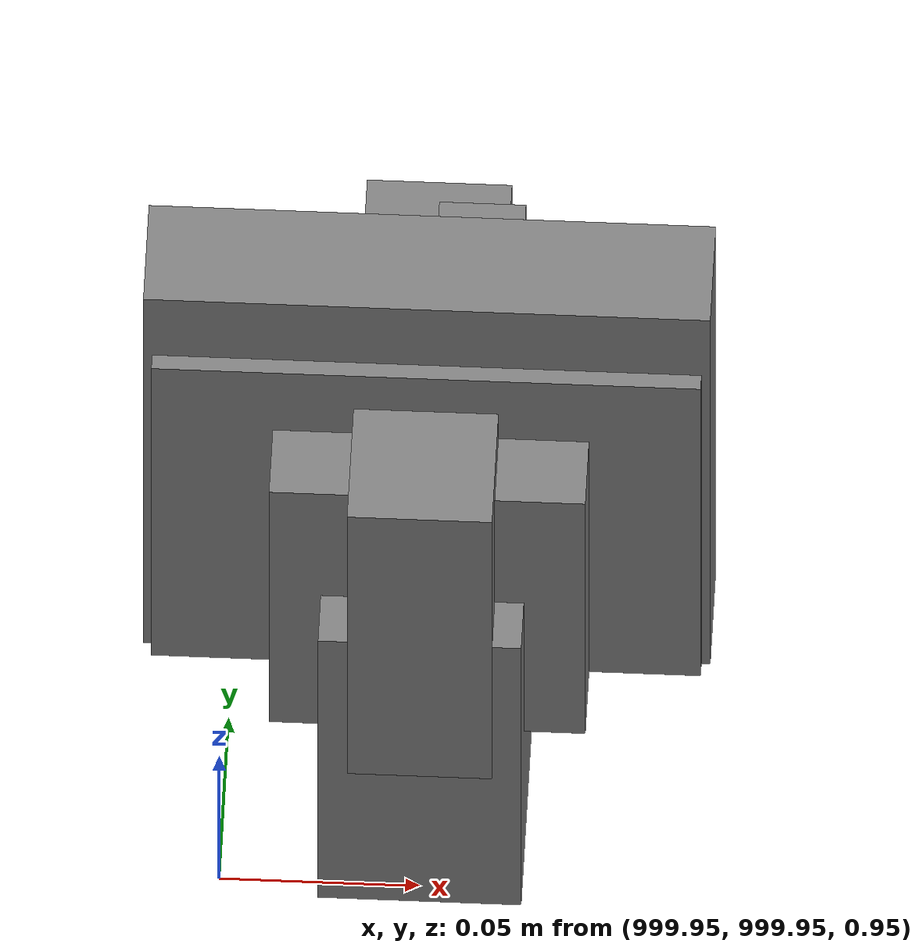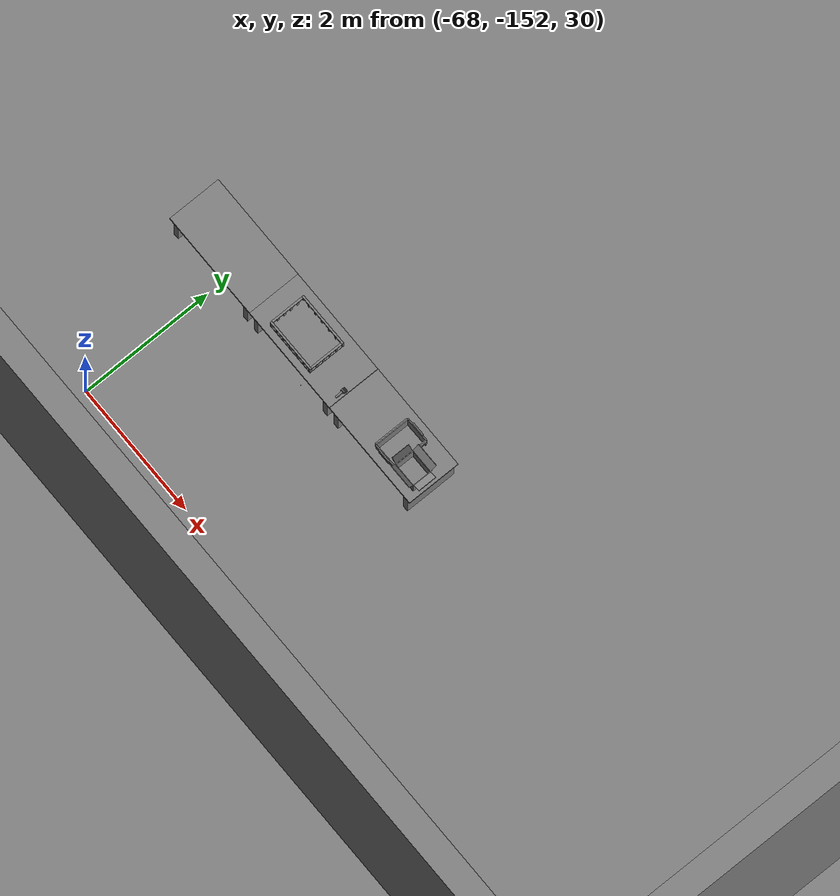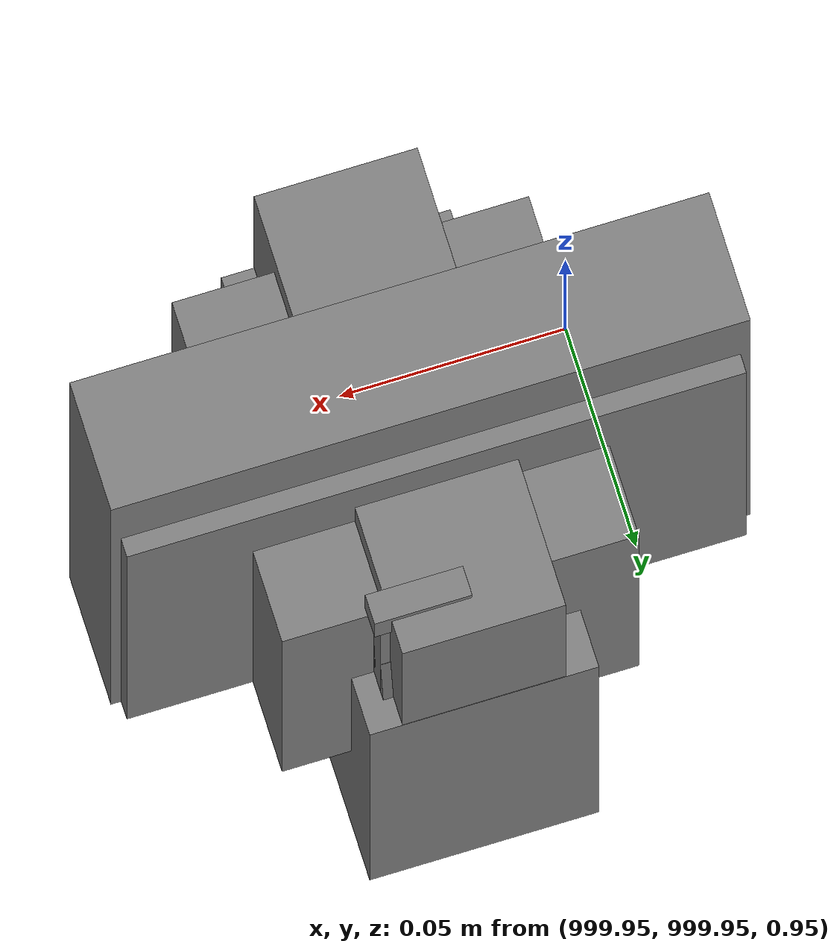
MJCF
<mujoco>
    <option gravity="0.000000000 0.000000000 -9.810000420" timestep="0.0049999999" integrator="implicitfast" density="1.225" viscosity="1.8000001e-05" noslip_iterations="10" iterations="100" sdf_iterations="50">
        <flag multiccd="disable"/>
    </option>
    <size memory="1000M"/>
    <compiler coordinate="local"/>
    <worldbody>
        <light cutoff="30" pos="0 1 1" dir="0 -1 -2"/>
        <light cutoff="30" pos="0 -1 1" dir="0 1 -2"/>
        <body pos="-66.137802124 -148.971618652 31.162263870" euler="-8.131485939 21.678848267 -106.022369385" mocap="true" name="spotlight4_SpotLight"/>
        <body pos="-66.366203308 -149.174697876 31.167335510" euler="22.138771057 35.985107422 -149.667037964" mocap="true" name="spotlight5_SpotLight"/>
        <body pos="1000.000000000 1000.000000000 1.000000000" euler="0.000000000 0.000000000 180.000000000" name="openloong_gripper_2f85_fix_base_usda_wifi_box">
            <geom contype="1" conaffinity="1" density="1000" type="box" material="" rgba="0.500000000 0.500000000 0.500000000 1.000000000" solimp="0.899999976 0.949999988 0.001000000" friction="1.000000000 0.005000000 0.000100000" solref="0.020000000 1.000000000" margin="0" condim="3" group="0" pos="0.000000000 0.000000000 0.058978677" quat="0.000000000 0.000000047 0.000000000 1.000000000" size="0.068499997 0.018999999 0.059000000" name="openloong_gripper_2f85_fix_base_usda_geom_130F029F_2C61_4CEC_A9E3_AC4E2A8282F0"/>
            <freejoint name="openloong_gripper_2f85_fix_base_usda_wifi_box_joint"/>
            <site size="0.005000000 0.005000000 0.005000000" rgba="0.500000000 0.500000000 0.500000000 1.000000000" pos="0.000000000 0.000000000 0.000000000" quat="0.999961913 0.008726500 0.000000000 0.000000000" group="0" type="sphere" name="openloong_gripper_2f85_fix_base_usda_wifi_boxsite"/>
        </body>
        <body pos="1000.000000000 1000.000000000 1.000000000" euler="0.000000000 0.000000000 180.000000000" name="openloong_gripper_2f85_fix_base_usda_battery_01">
            <geom contype="1" conaffinity="1" density="1000" type="box" material="" rgba="0.500000000 0.500000000 0.500000000 1.000000000" solimp="0.899999976 0.949999988 0.001000000" friction="1.000000000 0.005000000 0.000100000" solref="0.020000000 1.000000000" margin="0" condim="3" group="0" pos="-0.011123657 -0.041940309 0.101691343" quat="1.000000000 0.000000000 0.000000000 0.000000000" size="0.010800000 0.003375000 0.004725000" name="openloong_gripper_2f85_fix_base_usda_geom_0C534FF8_46CE_4B40_BE82_8F12F3BF3893"/>
            <geom contype="1" conaffinity="1" density="1000" type="box" material="" rgba="0.500000000 0.500000000 0.500000000 1.000000000" solimp="0.899999976 0.949999988 0.001000000" friction="1.000000000 0.005000000 0.000100000" solref="0.020000000 1.000000000" margin="0" condim="3" group="0" pos="-0.010876465 -0.044247437 0.047066893" quat="0.998702705 -0.050920475 0.000000000 0.000000000" size="0.009450001 0.002700000 0.024975000" name="openloong_gripper_2f85_fix_base_usda_geom_03225A2C_51ED_49EC_B36B_B23B7E80A911"/>
            <geom contype="1" conaffinity="1" density="1000" type="box" material="" rgba="0.500000000 0.500000000 0.500000000 1.000000000" solimp="0.899999976 0.949999988 0.001000000" friction="1.000000000 0.005000000 0.000100000" solref="0.020000000 1.000000000" margin="0" condim="3" group="0" pos="-0.001235962 -0.000659180 0.047381196" quat="1.000000000 0.000000000 0.000000000 0.000000000" size="0.039420001 0.039150000 0.047250003" name="openloong_gripper_2f85_fix_base_usda_geom_7B590F01_B788_4884_961B_B8C28BF7C23A"/>
            <geom contype="1" conaffinity="1" density="1000" type="box" material="" rgba="0.500000000 0.500000000 0.500000000 1.000000000" solimp="0.899999976 0.949999988 0.001000000" friction="1.000000000 0.005000000 0.000100000" solref="0.020000000 1.000000000" margin="0" condim="3" group="0" pos="-0.010876465 -0.039138794 0.009851727" quat="1.000000000 0.000000000 0.000000000 0.000000000" size="0.009450001 0.010800000 0.013500000" name="openloong_gripper_2f85_fix_base_usda_geom_711B4B94_ABCE_46B5_8CE5_95254C04E8E3"/>
            <geom contype="1" conaffinity="1" density="1000" type="box" material="" rgba="0.500000000 0.500000000 0.500000000 1.000000000" solimp="0.899999976 0.949999988 0.001000000" friction="1.000000000 0.005000000 0.000100000" solref="0.020000000 1.000000000" margin="0" condim="3" group="0" pos="-0.010876465 -0.041528322 0.071508206" quat="1.000000000 0.000000000 0.000000000 0.000000000" size="0.009450001 0.002700000 0.027000001" name="openloong_gripper_2f85_fix_base_usda_geom_679C6510_4A7E_449D_8C62_16AFA0C9EDBD"/>
            <freejoint name="openloong_gripper_2f85_fix_base_usda_battery_01_joint"/>
            <site size="0.005000000 0.005000000 0.005000000" rgba="0.500000000 0.500000000 0.500000000 1.000000000" pos="0.000000000 0.000000000 0.000000000" quat="0.999961913 0.008726500 0.000000000 0.000000000" group="0" type="sphere" name="openloong_gripper_2f85_fix_base_usda_battery_01site"/>
        </body>
        <body pos="-65.957466125 -149.002395630 31.166622162" euler="119.380775452 -54.928890228 -116.283256531" mocap="true" name="spotlight3_SpotLight"/>
        <body pos="1000.000000000 1000.000000000 1.000000000" euler="0.000000000 0.000000000 180.000000000" name="openloong_gripper_2f85_fix_base_usda_cpu_fan">
            <geom contype="1" conaffinity="1" density="1000" type="box" material="" rgba="0.500000000 0.500000000 0.500000000 1.000000000" solimp="0.899999976 0.949999988 0.001000000" friction="1.000000000 0.005000000 0.000100000" solref="0.020000000 1.000000000" margin="0" condim="3" group="0" pos="0.000000000 0.000000000 0.070034981" quat="0.000000000 0.000000000 0.000000000 1.000000000" size="0.070700005 0.014699999 0.070700005" name="openloong_gripper_2f85_fix_base_usda_geom_BED85670_77FF_4C2F_9836_31860768C117"/>
            <freejoint name="openloong_gripper_2f85_fix_base_usda_cpu_fan_joint"/>
            <site size="0.005000000 0.005000000 0.005000000" rgba="0.500000000 0.500000000 0.500000000 1.000000000" pos="0.000000000 0.000000000 0.000000000" quat="0.999961913 0.008726535 0.000000000 0.000000000" group="0" type="sphere" name="openloong_gripper_2f85_fix_base_usda_cpu_fancsite"/>
        </body>
        <body pos="1000.000000000 1000.000000000 1.000000000" euler="0.000011953 0.000005123 -179.999984741" name="openloong_gripper_2f85_fix_base_usda_intel_box">
            <geom contype="1" conaffinity="1" density="1000" type="box" material="" rgba="0.500000000 0.500000000 0.500000000 1.000000000" solimp="0.899999976 0.949999988 0.001000000" friction="1.000000000 0.005000000 0.000100000" solref="0.020000000 1.000000000" margin="0" condim="3" group="0" pos="0.000000000 -0.000067139 0.000082284" quat="0.707106709 0.000000225 0.000000253 0.707106650" size="0.052800003 0.025300000 0.052800003" name="openloong_gripper_2f85_fix_base_usda_geom_3AA7D898_B0C1_4C0F_B104_3DF3BBC20B43"/>
            <freejoint name="openloong_gripper_2f85_fix_base_usda_intel_box_joint"/>
            <site size="0.005000000 0.005000000 0.005000000" rgba="0.500000000 0.500000000 0.500000000 1.000000000" pos="0.000000000 0.000000000 0.000000000" quat="0.999961913 0.008726500 0.000000000 0.000000000" group="0" type="sphere" name="openloong_gripper_2f85_fix_base_usda_intel_boxsite"/>
        </body>
        <body pos="1000.000000000 999.999938965 1.000000000" euler="0.000000000 0.000000000 180.000000000" name="openloong_gripper_2f85_fix_base_usda_intelcore_i5">
            <geom contype="1" conaffinity="1" density="1000" type="box" material="" rgba="0.500000000 0.500000000 0.500000000 1.000000000" solimp="0.899999976 0.949999988 0.001000000" friction="1.000000000 0.005000000 0.000100000" solref="0.020000000 1.000000000" margin="0" condim="3" group="0" pos="0.000000000 0.000000000 0.051722717" quat="0.707106709 0.000000000 0.000000000 -0.707106769" size="0.052800000 0.018080002 0.052800000" name="openloong_gripper_2f85_fix_base_usda_geom_4FD43BCF_15DF_497C_BC42_7E6983528808"/>
            <freejoint name="openloong_gripper_2f85_fix_base_usda_intelcore_i5_joint"/>
            <site size="0.005000000 0.005000000 0.005000000" rgba="0.500000000 0.500000000 0.500000000 1.000000000" pos="0.000000000 0.000000000 0.000000000" quat="0.999961913 0.008726534 0.000000000 0.000000000" group="0" type="sphere" name="openloong_gripper_2f85_fix_base_usda_intelcore_i5site"/>
        </body>
        <body pos="-64.866622925 -149.383972168 30.183746338" euler="89.999984741 89.999946594 0.000000000" name="openloong_gripper_2f85_fix_base_usda_bluebox_01">
            <geom contype="1" conaffinity="1" density="1000" type="box" material="" rgba="0.500000000 0.500000000 0.500000000 1.000000000" solimp="0.899999976 0.949999988 0.001000000" friction="1.000000000 0.005000000 0.000100000" solref="0.020000000 1.000000000" margin="0" condim="3" group="0" pos="0.276580811 0.187225342 0.000068665" quat="0.707106948 0.000077471 0.707106352 0.000077486" size="0.100000001 0.057999998 0.010000000" name="openloong_gripper_2f85_fix_base_usda_geom_DD03ACD6_6001_4F12_8762_6830D92F7EFB"/>
            <geom contype="1" conaffinity="1" density="1000" type="box" material="" rgba="0.500000000 0.500000000 0.500000000 1.000000000" solimp="0.899999976 0.949999988 0.001000000" friction="1.000000000 0.005000000 0.000100000" solref="0.020000000 1.000000000" margin="0" condim="3" group="0" pos="0.000000000 0.002883911 0.000000000" quat="0.999999881 0.000000000 0.000000000 0.000000000" size="0.254000008 0.003000000 0.172000006" name="openloong_gripper_2f85_fix_base_usda_geom_20A7D32D_443E_43BD_83F0_959DF6A1D6BE"/>
            <geom contype="1" conaffinity="1" density="1000" type="box" material="" rgba="0.500000000 0.500000000 0.500000000 1.000000000" solimp="0.899999976 0.949999988 0.001000000" friction="1.000000000 0.005000000 0.000100000" solref="0.020000000 1.000000000" margin="0" condim="3" group="0" pos="0.000000000 0.124874115 0.173484802" quat="0.999796331 0.020176515 -0.000000015 0.000000030" size="0.259999990 0.119999997 0.007000000" name="openloong_gripper_2f85_fix_base_usda_geom_3D39A4C8_FE3D_4097_8B75_D737BC0B55FC"/>
            <geom contype="1" conaffinity="1" density="1000" type="box" material="" rgba="0.500000000 0.500000000 0.500000000 1.000000000" solimp="0.899999976 0.949999988 0.001000000" friction="1.000000000 0.005000000 0.000100000" solref="0.020000000 1.000000000" margin="0" condim="3" group="0" pos="0.000000000 0.124874115 -0.173469543" quat="0.999796331 -0.020176545 -0.000000015 0.000000000" size="0.259999990 0.119999997 0.007000000" name="openloong_gripper_2f85_fix_base_usda_geom_E46F80CF_BD21_49B5_8C29_2A0BABBBEC32"/>
            <geom contype="1" conaffinity="1" density="1000" type="box" material="" rgba="0.500000000 0.500000000 0.500000000 1.000000000" solimp="0.899999976 0.949999988 0.001000000" friction="1.000000000 0.005000000 0.000100000" solref="0.020000000 1.000000000" margin="0" condim="3" group="0" pos="0.000000000 0.214008331 0.188980103" quat="0.999912977 0.013176724 0.000000015 0.000000000" size="0.259999990 0.029999999 0.012500000" name="openloong_gripper_2f85_fix_base_usda_geom_D4ACDF6F_89DB_4DB7_AF6E_61108349D91A"/>
            <geom contype="1" conaffinity="1" density="1000" type="box" material="" rgba="0.500000000 0.500000000 0.500000000 1.000000000" solimp="0.899999976 0.949999988 0.001000000" friction="1.000000000 0.005000000 0.000100000" solref="0.020000000 1.000000000" margin="0" condim="3" group="0" pos="-0.258361816 0.125289917 0.001876831" quat="0.702796936 -0.020792112 0.710783124 0.020769298" size="0.189999998 0.119999997 0.009000000" name="openloong_gripper_2f85_fix_base_usda_geom_7507E245_581B_480A_822D_EDBACF4CA271"/>
            <geom contype="1" conaffinity="1" density="1000" type="box" material="" rgba="0.500000000 0.500000000 0.500000000 1.000000000" solimp="0.899999976 0.949999988 0.001000000" friction="1.000000000 0.005000000 0.000100000" solref="0.020000000 1.000000000" margin="0" condim="3" group="0" pos="0.000000000 0.214008331 -0.188980103" quat="0.999912977 -0.013176769 0.000000030 0.000000015" size="0.259999990 0.029999999 0.012500000" name="openloong_gripper_2f85_fix_base_usda_geom_5BAB27D7_9924_4D61_90E0_B6E6C6451435"/>
            <geom contype="1" conaffinity="1" density="1000" type="box" material="" rgba="0.500000000 0.500000000 0.500000000 1.000000000" solimp="0.899999976 0.949999988 0.001000000" friction="1.000000000 0.005000000 0.000100000" solref="0.020000000 1.000000000" margin="0" condim="3" group="0" pos="-0.276611328 0.187225342 0.000068665" quat="0.707106650 0.000077441 0.707106709 0.000077456" size="0.100000001 0.057999998 0.010000000" name="openloong_gripper_2f85_fix_base_usda_geom_B4FC2334_53D8_439E_9578_7D5A19C85035"/>
            <geom contype="1" conaffinity="1" density="1000" type="box" material="" rgba="0.500000000 0.500000000 0.500000000 1.000000000" solimp="0.899999976 0.949999988 0.001000000" friction="1.000000000 0.005000000 0.000100000" solref="0.020000000 1.000000000" margin="0" condim="3" group="0" pos="0.258331299 0.125289917 0.001876831" quat="0.702851415 0.018856421 0.710823774 -0.019329369" size="0.189999998 0.119999997 0.009000000" name="openloong_gripper_2f85_fix_base_usda_geom_9D60638E_4530_4853_A72F_B8D19560AEB6"/>
            <freejoint name="openloong_gripper_2f85_fix_base_usda_bluebox_01_joint"/>
            <site size="0.005000000 0.005000000 0.005000000" rgba="0.500000000 0.500000000 0.500000000 1.000000000" pos="0.000000000 0.000000000 0.000000000" quat="0.999961913 0.008726534 0.000000000 0.000000000" group="0" type="sphere" name="openloong_gripper_2f85_fix_base_usda_bluebox_01site"/>
        </body>
        <body pos="-64.496299744 -149.491867065 30.235729218" euler="0.000000000 0.000000000 89.999946594" name="openloong_gripper_2f85_fix_base_usda_cardboardbox_01">
            <geom contype="1" conaffinity="1" density="1000" type="box" material="" rgba="0.500000000 0.500000000 0.500000000 1.000000000" solimp="0.899999976 0.949999988 0.001000000" friction="1.000000000 0.005000000 0.000100000" solref="0.020000000 1.000000000" margin="0" condim="3" group="0" pos="-0.003166199 -0.004086494 0.005052090" quat="1.000000000 0.000000000 0.000000000 0.000000000" size="0.142499998 0.177500010 0.005000000" name="openloong_gripper_2f85_fix_base_usda_geom_59585F68_949E_45FD_8A99_1BAA9C32F134"/>
            <geom contype="1" conaffinity="1" density="1000" type="box" material="" rgba="0.500000000 0.500000000 0.500000000 1.000000000" solimp="0.899999976 0.949999988 0.001000000" friction="1.000000000 0.005000000 0.000100000" solref="0.020000000 1.000000000" margin="0" condim="3" group="0" pos="-0.003166199 0.170316696 0.150570869" quat="1.000000000 0.000000000 0.000000000 0.000000000" size="0.142499998 0.005000000 0.149999991" name="openloong_gripper_2f85_fix_base_usda_geom_F7565B7F_C21A_48F7_A340_A15AA0199F3A"/>
            <geom contype="1" conaffinity="1" density="1000" type="box" material="" rgba="0.500000000 0.500000000 0.500000000 1.000000000" solimp="0.899999976 0.949999988 0.001000000" friction="1.000000000 0.005000000 0.000100000" solref="0.020000000 1.000000000" margin="0" condim="3" group="0" pos="-0.147399902 -0.005307198 0.150570869" quat="1.000000000 0.000000000 0.000000000 0.000000000" size="0.005000000 0.177500010 0.149999991" name="openloong_gripper_2f85_fix_base_usda_geom_DB59AC59_41D9_4F3A_B458_5D0DCC2FA8EC"/>
            <geom contype="1" conaffinity="1" density="1000" type="box" material="" rgba="0.500000000 0.500000000 0.500000000 1.000000000" solimp="0.899999976 0.949999988 0.001000000" friction="1.000000000 0.005000000 0.000100000" solref="0.020000000 1.000000000" margin="0" condim="3" group="0" pos="0.140275955 -0.005307198 0.150570869" quat="1.000000000 0.000000000 0.000000000 0.000000000" size="0.005000000 0.177500010 0.149999991" name="openloong_gripper_2f85_fix_base_usda_geom_03485629_3705_48D8_877D_4EFC7A235A8C"/>
            <geom contype="1" conaffinity="1" density="1000" type="box" material="" rgba="0.500000000 0.500000000 0.500000000 1.000000000" solimp="0.899999976 0.949999988 0.001000000" friction="1.000000000 0.005000000 0.000100000" solref="0.020000000 1.000000000" margin="0" condim="3" group="0" pos="-0.003166199 -0.181550980 0.150570869" quat="1.000000000 0.000000000 0.000000000 0.000000000" size="0.142499998 0.005000000 0.149999991" name="openloong_gripper_2f85_fix_base_usda_geom_2836677E_62FB_411E_B94D_CD9B6E2C1378"/>
            <freejoint name="openloong_gripper_2f85_fix_base_usda_cardboardbox_01_joint"/>
            <site size="0.005000000 0.005000000 0.005000000" rgba="0.500000000 0.500000000 0.500000000 1.000000000" pos="0.000000000 0.000000000 0.000000000" quat="0.999961913 0.008726535 0.000000000 0.000000000" group="0" type="sphere" name="openloong_gripper_2f85_fix_base_usda_site_E09E0F30_8357_4FFF_8678_2C24BB13BCA0"/>
            <body pos="0.139160156 -0.004048347 0.301930904" euler="-179.999954224 49.383502960 179.999954224" name="openloong_gripper_2f85_fix_base_usda_A1_006">
                <geom contype="1" conaffinity="1" density="1000" type="box" material="" rgba="0.500000000 0.500000000 0.500000000 1.000000000" solimp="0.899999976 0.949999988 0.001000000" friction="1.000000000 0.005000000 0.000100000" solref="0.020000000 1.000000000" margin="0" condim="3" group="0" pos="-0.071587563 0.000009537 0.001745224" quat="0.999999881 0.000000000 0.000000000 0.000000000" size="0.071249999 0.179999992 0.002500000" name="openloong_gripper_2f85_fix_base_usda_geom_96D01E6A_E09C_4DDD_BC4C_58A367404FF0"/>
                <joint armature="0" stiffness="0.07" damping="0.0099999998" axis="0.000000 1.000000 0.000000" type="hinge" name="openloong_gripper_2f85_fix_base_usda_A1_006"/>
            </body>
            <body pos="-0.145902634 -0.004086494 0.301938057" euler="-180.000000000 -60.000011444 -180.000000000" name="openloong_gripper_2f85_fix_base_usda_A2_006">
                <geom contype="1" conaffinity="1" density="1000" type="box" material="" rgba="0.500000000 0.500000000 0.500000000 1.000000000" solimp="0.899999976 0.949999988 0.001000000" friction="1.000000000 0.005000000 0.000100000" solref="0.020000000 1.000000000" margin="0" condim="3" group="0" pos="0.071268082 0.000009537 0.002717972" quat="0.000002921 0.000000000 -0.000000030 0.999999881" size="0.071249999 0.179999992 0.002500000" name="openloong_gripper_2f85_fix_base_usda_geom_7C03B603_2482_491B_8825_FC0FFFC9AB56"/>
                <joint armature="0" stiffness="0.07" damping="0.0099999998" axis="0.000000 1.000000 0.000000" type="hinge" name="openloong_gripper_2f85_fix_base_usda_A2_006"/>
            </body>
            <body pos="-0.003385544 0.175991058 0.301930904" euler="-125.858116150 -0.000004561 0.000002331" name="openloong_gripper_2f85_fix_base_usda_B2_006">
                <geom contype="1" conaffinity="1" density="1000" type="box" material="" rgba="0.500000000 0.500000000 0.500000000 1.000000000" solimp="0.899999976 0.949999988 0.001000000" friction="1.000000000 0.005000000 0.000100000" solref="0.020000000 1.000000000" margin="0" condim="3" group="0" pos="0.000009537 -0.070939064 -0.002470016" quat="0.999614120 0.027776197 -0.000000015 0.000000030" size="0.137500003 0.064999998 0.005000000" name="openloong_gripper_2f85_fix_base_usda_geom_DF0DE728_066C_49B5_ADA0_56EA689A7CF1"/>
                <joint armature="0" stiffness="0.07" damping="0.0099999998" axis="1.000000 0.000000 0.000000" type="hinge" name="openloong_gripper_2f85_fix_base_usda_B2_006"/>
            </body>
            <body pos="-0.003385544 -0.184140205 0.301938057" euler="147.805557251 0.000000000 0.000000000" name="openloong_gripper_2f85_fix_base_usda_B1_006">
                <geom contype="1" conaffinity="1" density="1000" type="box" material="" rgba="0.500000000 0.500000000 0.500000000 1.000000000" solimp="0.899999976 0.949999988 0.001000000" friction="1.000000000 0.005000000 0.000100000" solref="0.020000000 1.000000000" margin="0" condim="3" group="0" pos="-0.000028610 0.070202351 -0.002703667" quat="0.999614179 -0.027776167 0.000000000 0.000000000" size="0.137500003 0.064999998 0.005000000" name="openloong_gripper_2f85_fix_base_usda_geom_67FE1BD9_3BD0_4E96_87EF_0A6D4B4CD588"/>
                <joint armature="0" stiffness="0.07" damping="0.0099999998" axis="1.000000 0.000000 0.000000" type="hinge" name="openloong_gripper_2f85_fix_base_usda_B1_006"/>
            </body>
        </body>
        <body pos="-65.882858276 -149.481979370 30.229999542" euler="-64.487716675 0.000000000 0.000000000" name="openloong_gripper_2f85_fix_base_usda_Barcode">
            <geom contype="1" conaffinity="1" density="1000" type="box" material="" rgba="0.500000000 0.500000000 0.500000000 1.000000000" solimp="0.899999976 0.949999988 0.001000000" friction="1.000000000 0.005000000 0.000100000" solref="0.020000000 1.000000000" margin="0" condim="3" group="0" pos="0.000000000 0.013038635 0.001419067" quat="0.000000000 0.000000000 0.000000000 1.000000119" size="0.034000002 0.010000000 0.017999999" name="openloong_gripper_2f85_fix_base_usda_geom_2C3885E4_DD9C_438A_A75C_4255CE29E922"/>
            <geom contype="1" conaffinity="1" density="1000" type="box" material="" rgba="0.500000000 0.500000000 0.500000000 1.000000000" solimp="0.899999976 0.949999988 0.001000000" friction="1.000000000 0.005000000 0.000100000" solref="0.020000000 1.000000000" margin="0" condim="3" group="0" pos="0.000000000 -0.035301208 -0.007095337" quat="0.000000000 0.000000000 -0.043619365 0.999048233" size="0.028999999 0.010000000 0.020000000" name="openloong_gripper_2f85_fix_base_usda_geom_BAE1882A_287F_4D14_9697_A2A5B209308A"/>
            <geom contype="1" conaffinity="1" density="1000" type="box" material="" rgba="0.500000000 0.500000000 0.500000000 1.000000000" solimp="0.899999976 0.949999988 0.001000000" friction="1.000000000 0.005000000 0.000100000" solref="0.020000000 1.000000000" margin="0" condim="3" group="0" pos="0.000000000 -0.043411255 -0.011749268" quat="0.922262907 0.386563420 0.000000000 0.000000000" size="0.026000001 0.010000000 0.020000000" name="openloong_gripper_2f85_fix_base_usda_geom_7BCE995B_E208_4459_9F63_D3ACEC615FF8"/>
            <geom contype="1" conaffinity="1" density="1000" type="box" material="" rgba="0.500000000 0.500000000 0.500000000 1.000000000" solimp="0.899999976 0.949999988 0.001000000" friction="1.000000000 0.005000000 0.000100000" solref="0.020000000 1.000000000" margin="0" condim="3" group="0" pos="0.000000000 -0.016967773 -0.031860352" quat="0.000000000 0.000000000 0.000000000 1.000000119" size="0.008000000 0.010000000 0.013000000" name="openloong_gripper_2f85_fix_base_usda_geom_051356B9_47FD_48E2_BDE9_3012FA78B3F7"/>
            <geom contype="1" conaffinity="1" density="1000" type="box" material="" rgba="0.500000000 0.500000000 0.500000000 1.000000000" solimp="0.899999976 0.949999988 0.001000000" friction="1.000000000 0.005000000 0.000100000" solref="0.020000000 1.000000000" margin="0" condim="3" group="0" pos="0.000000000 -0.001869202 0.000312805" quat="0.953716993 0.300705761 0.000000000 0.000000000" size="0.032000002 0.010000000 0.018999999" name="openloong_gripper_2f85_fix_base_usda_geom_65EA5362_1CB7_4BFB_A6FE_37C464515062"/>
            <geom contype="1" conaffinity="1" density="1000" type="box" material="" rgba="0.500000000 0.500000000 0.500000000 1.000000000" solimp="0.899999976 0.949999988 0.001000000" friction="1.000000000 0.005000000 0.000100000" solref="0.020000000 1.000000000" margin="0" condim="3" group="0" pos="0.000000000 -0.019531250 -0.003173828" quat="0.953716993 0.300705761 0.000000000 0.000000000" size="0.030999999 0.010000000 0.020000000" name="openloong_gripper_2f85_fix_base_usda_geom_E6BA1ECA_6A72_4DAF_9598_7F407E3E4FA6"/>
            <geom contype="1" conaffinity="1" density="1000" type="box" material="" rgba="0.500000000 0.500000000 0.500000000 1.000000000" solimp="0.899999976 0.949999988 0.001000000" friction="1.000000000 0.005000000 0.000100000" solref="0.020000000 1.000000000" margin="0" condim="3" group="0" pos="0.000000000 -0.035301208 -0.007095337" quat="0.953716993 0.300705761 0.000000000 0.000000000" size="0.028999999 0.010000000 0.020000000" name="openloong_gripper_2f85_fix_base_usda_geom_B368ED46_A156_4D55_A3DC_C3B29D49CF8D"/>
            <geom contype="1" conaffinity="1" density="1000" type="box" material="" rgba="0.500000000 0.500000000 0.500000000 1.000000000" solimp="0.899999976 0.949999988 0.001000000" friction="1.000000000 0.005000000 0.000100000" solref="0.020000000 1.000000000" margin="0" condim="3" group="0" pos="0.000000000 -0.042617798 -0.071121216" quat="0.000000000 0.000000000 0.000000000 1.000000119" size="0.013000000 0.021000000 0.059999999" name="openloong_gripper_2f85_fix_base_usda_geom_5C5598FF_FCD7_4CE6_A546_D5988DBE9F92"/>
            <freejoint name="openloong_gripper_2f85_fix_base_usda_Barcode_joint"/>
            <site size="0.005000000 0.005000000 0.005000000" rgba="0.500000000 0.500000000 0.500000000 1.000000000" pos="0.000000000 0.000000000 0.000000000" quat="1.000000000 0.000000000 0.000000000 0.000000000" group="0" type="sphere" name="openloong_gripper_2f85_fix_base_usda_Barcode_site"/>
        </body>
        <body pos="-66.745018005 -149.392349243 30.184000015" euler="0.000000000 0.000000000 89.999946594" name="[22331275775640]_Basket_01">
            <geom contype="1" conaffinity="1" density="1000" type="box" material="" rgba="0.500000000 0.500000000 0.500000000 1.000000000" solimp="0.899999976 0.949999988 0.001000000" friction="1.000000000 0.005000000 0.000100000" solref="0.020000000 1.000000000" margin="0" condim="3" group="0" pos="-0.052425385 0.389207840 0.089787483" quat="0.707107008 0.000000000 0.000000000 0.707106411" size="0.014249999 0.014249999 0.059999999" name="[22331275775640]_geom_DB7A3B08_AB30_4239_B233_BF12D1099556"/>
            <geom contype="1" conaffinity="1" density="1000" type="box" material="" rgba="0.500000000 0.500000000 0.500000000 1.000000000" solimp="0.899999976 0.949999988 0.001000000" friction="1.000000000 0.005000000 0.000100000" solref="0.020000000 1.000000000" margin="0" condim="3" group="0" pos="0.264015198 -0.133043289 0.089787483" quat="0.707107008 0.000000000 0.000000000 0.707106411" size="0.014249999 0.014249999 0.059999999" name="[22331275775640]_geom_F0CE8241_2439_4E35_A123_F57CA20DAA45"/>
            <geom contype="1" conaffinity="1" density="1000" type="box" material="" rgba="0.500000000 0.500000000 0.500000000 1.000000000" solimp="0.899999976 0.949999988 0.001000000" friction="1.000000000 0.005000000 0.000100000" solref="0.020000000 1.000000000" margin="0" condim="3" group="0" pos="-0.264015198 -0.265548706 0.089793205" quat="0.707107008 0.000000000 0.000000000 0.707106411" size="0.014249999 0.014249999 0.059999999" name="[22331275775640]_geom_A7399CA6_D160_405A_A476_4FC94DBDC1C8"/>
            <geom contype="1" conaffinity="1" density="1000" type="box" material="" rgba="0.500000000 0.500000000 0.500000000 1.000000000" solimp="0.899999976 0.949999988 0.001000000" friction="1.000000000 0.005000000 0.000100000" solref="0.020000000 1.000000000" margin="0" condim="3" group="0" pos="-0.160263062 -0.389322281 0.089793205" quat="0.707107008 0.000000000 0.000000000 0.707106411" size="0.014249999 0.014249999 0.059999999" name="[22331275775640]_geom_99221157_FD52_4C3E_9162_40A9FDE87911"/>
            <geom contype="1" conaffinity="1" density="1000" type="box" material="" rgba="0.500000000 0.500000000 0.500000000 1.000000000" solimp="0.899999976 0.949999988 0.001000000" friction="1.000000000 0.005000000 0.000100000" solref="0.020000000 1.000000000" margin="0" condim="3" group="0" pos="0.162265778 -0.389322281 0.089787483" quat="0.707107008 0.000000000 0.000000000 0.707106411" size="0.014249999 0.014249999 0.059999999" name="[22331275775640]_geom_F2FEF71A_F84B_42BB_8E91_91309A349A4B"/>
            <geom contype="1" conaffinity="1" density="1000" type="box" material="" rgba="0.500000000 0.500000000 0.500000000 1.000000000" solimp="0.899999976 0.949999988 0.001000000" friction="1.000000000 0.005000000 0.000100000" solref="0.020000000 1.000000000" margin="0" condim="3" group="0" pos="0.264015198 0.389207840 0.089787483" quat="0.707107008 0.000000000 0.000000000 0.707106411" size="0.014249999 0.014249999 0.059999999" name="[22331275775640]_geom_2388E69C_8390_4BD4_8178_908DB433662A"/>
            <geom contype="1" conaffinity="1" density="1000" type="box" material="" rgba="0.500000000 0.500000000 0.500000000 1.000000000" solimp="0.899999976 0.949999988 0.001000000" friction="1.000000000 0.005000000 0.000100000" solref="0.020000000 1.000000000" margin="0" condim="3" group="0" pos="-0.264015198 -0.133043289 0.089793205" quat="0.707107008 0.000000000 0.000000000 0.707106411" size="0.014249999 0.014249999 0.059999999" name="[22331275775640]_geom_4B27E905_B636_4485_A249_ACC3EE558B21"/>
            <geom contype="1" conaffinity="1" density="1000" type="box" material="" rgba="0.500000000 0.500000000 0.500000000 1.000000000" solimp="0.899999976 0.949999988 0.001000000" friction="1.000000000 0.005000000 0.000100000" solref="0.020000000 1.000000000" margin="0" condim="3" group="0" pos="-0.264026642 0.269256592 0.089793205" quat="0.707107008 0.000000000 0.000000000 0.707106411" size="0.014249999 0.014249999 0.059999999" name="[22331275775640]_geom_52BF05E0_ACC6_4118_A9D8_A642E4FB8D76"/>
            <geom contype="1" conaffinity="1" density="1000" type="box" material="" rgba="0.500000000 0.500000000 0.500000000 1.000000000" solimp="0.899999976 0.949999988 0.001000000" friction="1.000000000 0.005000000 0.000100000" solref="0.020000000 1.000000000" margin="0" condim="3" group="0" pos="0.054462433 0.389207840 0.089787483" quat="0.707107008 0.000000000 0.000000000 0.707106411" size="0.014249999 0.014249999 0.059999999" name="[22331275775640]_geom_1094CA32_785C_4077_82F5_C6069070F664"/>
            <geom contype="1" conaffinity="1" density="1000" type="box" material="" rgba="0.500000000 0.500000000 0.500000000 1.000000000" solimp="0.899999976 0.949999988 0.001000000" friction="1.000000000 0.005000000 0.000100000" solref="0.020000000 1.000000000" margin="0" condim="3" group="0" pos="0.054462433 -0.389322281 0.089787483" quat="0.707107008 0.000000000 0.000000000 0.707106411" size="0.014249999 0.014249999 0.059999999" name="[22331275775640]_geom_671CD279_72CD_4349_B67A_37A5DD2BACE7"/>
            <geom contype="1" conaffinity="1" density="1000" type="box" material="" rgba="0.500000000 0.500000000 0.500000000 1.000000000" solimp="0.899999976 0.949999988 0.001000000" friction="1.000000000 0.005000000 0.000100000" solref="0.020000000 1.000000000" margin="0" condim="3" group="0" pos="0.264015198 0.269256592 0.089793205" quat="0.707107008 0.000000000 0.000000000 0.707106411" size="0.014249999 0.014249999 0.059999999" name="[22331275775640]_geom_90319879_928D_49F2_9AE8_2D50CE1D5695"/>
            <geom contype="1" conaffinity="1" density="1000" type="box" material="" rgba="0.500000000 0.500000000 0.500000000 1.000000000" solimp="0.899999976 0.949999988 0.001000000" friction="1.000000000 0.005000000 0.000100000" solref="0.020000000 1.000000000" margin="0" condim="3" group="0" pos="0.264015198 -0.389322281 0.089787483" quat="0.707107008 0.000000000 0.000000000 0.707106411" size="0.014249999 0.014249999 0.059999999" name="[22331275775640]_geom_2E6FD15E_C43C_47E0_8CA8_003D81EAEBB0"/>
            <geom contype="1" conaffinity="1" density="1000" type="box" material="" rgba="0.500000000 0.500000000 0.500000000 1.000000000" solimp="0.899999976 0.949999988 0.001000000" friction="1.000000000 0.005000000 0.000100000" solref="0.020000000 1.000000000" margin="0" condim="3" group="0" pos="0.000000000 0.000000000 0.015998840" quat="0.707107008 0.000000000 0.000000000 0.707106411" size="0.403499991 0.279000014 0.015750000" name="[22331275775640]_geom_884F1573_8296_4032_B769_EC700F5172E7"/>
            <geom contype="1" conaffinity="1" density="1000" type="box" material="" rgba="0.500000000 0.500000000 0.500000000 1.000000000" solimp="0.899999976 0.949999988 0.001000000" friction="1.000000000 0.005000000 0.000100000" solref="0.020000000 1.000000000" margin="0" condim="3" group="0" pos="0.000000000 -0.389476776 0.163619041" quat="0.707107008 0.000000000 0.000000000 0.707106411" size="0.015000000 0.277500004 0.015750000" name="[22331275775640]_geom_C5D5CE49_521E_4F26_8CED_9D69D83285B3"/>
            <geom contype="1" conaffinity="1" density="1000" type="box" material="" rgba="0.500000000 0.500000000 0.500000000 1.000000000" solimp="0.899999976 0.949999988 0.001000000" friction="1.000000000 0.005000000 0.000100000" solref="0.020000000 1.000000000" margin="0" condim="3" group="0" pos="0.162265778 0.389207840 0.089787483" quat="0.707107008 0.000000000 0.000000000 0.707106411" size="0.014249999 0.014249999 0.059999999" name="[22331275775640]_geom_824FBBA0_79B1_4BED_8F55_2C7B0ACA2558"/>
            <geom contype="1" conaffinity="1" density="1000" type="box" material="" rgba="0.500000000 0.500000000 0.500000000 1.000000000" solimp="0.899999976 0.949999988 0.001000000" friction="1.000000000 0.005000000 0.000100000" solref="0.020000000 1.000000000" margin="0" condim="3" group="0" pos="0.000000000 0.389471054 0.163619041" quat="0.707107008 0.000000000 0.000000000 0.707106411" size="0.015000000 0.277500004 0.015750000" name="[22331275775640]_geom_CE319F9B_F7A5_4E49_A1E4_C29A0FC154BC"/>
            <geom contype="1" conaffinity="1" density="1000" type="box" material="" rgba="0.500000000 0.500000000 0.500000000 1.000000000" solimp="0.899999976 0.949999988 0.001000000" friction="1.000000000 0.005000000 0.000100000" solref="0.020000000 1.000000000" margin="0" condim="3" group="0" pos="-0.263511658 0.000000000 0.163619041" quat="0.707107008 0.000000000 0.000000000 0.707106411" size="0.403499991 0.015000000 0.015750000" name="[22331275775640]_geom_659BDBA6_9FB6_4A97_9E8F_BAB26D844E0E"/>
            <geom contype="1" conaffinity="1" density="1000" type="box" material="" rgba="0.500000000 0.500000000 0.500000000 1.000000000" solimp="0.899999976 0.949999988 0.001000000" friction="1.000000000 0.005000000 0.000100000" solref="0.020000000 1.000000000" margin="0" condim="3" group="0" pos="-0.264015198 0.141334534 0.089793205" quat="0.707107008 0.000000000 0.000000000 0.707106411" size="0.014249999 0.014249999 0.059999999" name="[22331275775640]_geom_11819E24_8279_466C_A91C_F72E525A99B7"/>
            <geom contype="1" conaffinity="1" density="1000" type="box" material="" rgba="0.500000000 0.500000000 0.500000000 1.000000000" solimp="0.899999976 0.949999988 0.001000000" friction="1.000000000 0.005000000 0.000100000" solref="0.020000000 1.000000000" margin="0" condim="3" group="0" pos="0.264015198 -0.265548706 0.089787483" quat="0.707107008 0.000000000 0.000000000 0.707106411" size="0.014249999 0.014249999 0.059999999" name="[22331275775640]_geom_7667F17E_1CDE_41E8_9DC6_2B59538106F5"/>
            <geom contype="1" conaffinity="1" density="1000" type="box" material="" rgba="0.500000000 0.500000000 0.500000000 1.000000000" solimp="0.899999976 0.949999988 0.001000000" friction="1.000000000 0.005000000 0.000100000" solref="0.020000000 1.000000000" margin="0" condim="3" group="0" pos="-0.160263062 0.389207840 0.089787483" quat="0.707107008 0.000000000 0.000000000 0.707106411" size="0.014249999 0.014249999 0.059999999" name="[22331275775640]_geom_6C3036CB_CA7F_49B6_8E35_3595EF11E302"/>
            <geom contype="1" conaffinity="1" density="1000" type="box" material="" rgba="0.500000000 0.500000000 0.500000000 1.000000000" solimp="0.899999976 0.949999988 0.001000000" friction="1.000000000 0.005000000 0.000100000" solref="0.020000000 1.000000000" margin="0" condim="3" group="0" pos="-0.052425385 -0.389322281 0.089787483" quat="0.707107008 0.000000000 0.000000000 0.707106411" size="0.014249999 0.014249999 0.059999999" name="[22331275775640]_geom_3B063493_E996_4B9D_8861_7ACF54BAEB02"/>
            <geom contype="1" conaffinity="1" density="1000" type="box" material="" rgba="0.500000000 0.500000000 0.500000000 1.000000000" solimp="0.899999976 0.949999988 0.001000000" friction="1.000000000 0.005000000 0.000100000" solref="0.020000000 1.000000000" margin="0" condim="3" group="0" pos="-0.264026642 -0.389322281 0.089793205" quat="0.707107008 0.000000000 0.000000000 0.707106411" size="0.014249999 0.014249999 0.059999999" name="[22331275775640]_geom_F203227C_E572_4CD8_A00A_6CAA8826B1BD"/>
            <geom contype="1" conaffinity="1" density="1000" type="box" material="" rgba="0.500000000 0.500000000 0.500000000 1.000000000" solimp="0.899999976 0.949999988 0.001000000" friction="1.000000000 0.005000000 0.000100000" solref="0.020000000 1.000000000" margin="0" condim="3" group="0" pos="0.264015198 0.141334534 0.089787483" quat="0.707107008 0.000000000 0.000000000 0.707106411" size="0.014249999 0.014249999 0.059999999" name="[22331275775640]_geom_5764F146_041F_401E_A004_CE39E248A408"/>
            <geom contype="1" conaffinity="1" density="1000" type="box" material="" rgba="0.500000000 0.500000000 0.500000000 1.000000000" solimp="0.899999976 0.949999988 0.001000000" friction="1.000000000 0.005000000 0.000100000" solref="0.020000000 1.000000000" margin="0" condim="3" group="0" pos="-0.264015198 0.389207840 0.089793205" quat="0.707107008 0.000000000 0.000000000 0.707106411" size="0.014249999 0.014249999 0.059999999" name="[22331275775640]_geom_71087D1E_D8C2_4388_9A61_BD79314F0952"/>
            <geom contype="1" conaffinity="1" density="1000" type="box" material="" rgba="0.500000000 0.500000000 0.500000000 1.000000000" solimp="0.899999976 0.949999988 0.001000000" friction="1.000000000 0.005000000 0.000100000" solref="0.020000000 1.000000000" margin="0" condim="3" group="0" pos="0.264015198 0.004480362 0.089787483" quat="0.707107008 0.000000000 0.000000000 0.707106411" size="0.014249999 0.014249999 0.059999999" name="[22331275775640]_geom_483EB640_EC28_414A_8FBF_EDA190B80B18"/>
            <geom contype="1" conaffinity="1" density="1000" type="box" material="" rgba="0.500000000 0.500000000 0.500000000 1.000000000" solimp="0.899999976 0.949999988 0.001000000" friction="1.000000000 0.005000000 0.000100000" solref="0.020000000 1.000000000" margin="0" condim="3" group="0" pos="0.263694763 -0.000011444 0.163619041" quat="0.707107008 0.000000000 0.000000000 0.707106411" size="0.403499991 0.015000000 0.015750000" name="[22331275775640]_geom_D59A7438_4E21_410A_9060_483385A48104"/>
            <geom contype="1" conaffinity="1" density="1000" type="box" material="" rgba="0.500000000 0.500000000 0.500000000 1.000000000" solimp="0.899999976 0.949999988 0.001000000" friction="1.000000000 0.005000000 0.000100000" solref="0.020000000 1.000000000" margin="0" condim="3" group="0" pos="-0.264015198 0.004480362 0.089793205" quat="0.707107008 0.000000000 0.000000000 0.707106411" size="0.014249999 0.014249999 0.059999999" name="[22331275775640]_geom_A9BCFFDC_D6ED_46AA_A918_A0ADF806AC3A"/>
            <freejoint name="[22331275775640]_joint_83C96FF2_6008_45E5_B4F6_713887D82862"/>
        </body>
        <body pos="0.000000000 0.000000000 0.000000000" euler="0.000000000 0.000000000 0.000000000" name="Static Objects_Static Objects">
            <geom contype="1" conaffinity="1" density="1000" type="box" material="" rgba="0.500000000 0.500000000 0.500000000 1.000000000" solimp="0.899999976 0.949999988 0.001000000" friction="1.000000000 0.005000000 0.000100000" solref="0.020000000 1.000000000" margin="0" condim="3" group="0" pos="-67.544113159 -149.365814209 29.727830887" quat="0.500000417 0.499999970 0.499999553 0.499999970" size="0.381000012 0.319999993 0.041000001" name="Static Objects_geom_AE9EAAE6_FCD0_4637_BD1E_12F58943E045"/>
            <geom contype="1" conaffinity="1" density="1000" type="box" material="" rgba="0.500000000 0.500000000 0.500000000 1.000000000" solimp="0.899999976 0.949999988 0.001000000" friction="1.000000000 0.005000000 0.000100000" solref="0.020000000 1.000000000" margin="0" condim="3" group="0" pos="-68.239501953 -149.365814209 30.086868286" quat="0.500000417 0.499999970 0.499999553 0.499999970" size="0.370999992 0.039500002 0.745000005" name="Static Objects_geom_2AB4DCB4_07BC_466D_AD61_A3EB977DAFEB"/>
            <geom contype="1" conaffinity="1" density="1000" type="box" material="" rgba="0.500000000 0.500000000 0.500000000 1.000000000" solimp="0.899999976 0.949999988 0.001000000" friction="1.000000000 0.005000000 0.000100000" solref="0.020000000 1.000000000" margin="0" condim="3" group="0" pos="-68.239501953 -149.365814209 30.147235870" quat="0.500000417 0.499999970 0.499999553 0.499999970" size="0.400000006 0.022000000 0.800000012" name="Static Objects_geom_57323E59_3C41_42E9_A29C_D5B47F914BC8"/>
            <geom contype="1" conaffinity="1" density="1000" type="box" material="" rgba="0.500000000 0.500000000 0.500000000 1.000000000" solimp="0.899999976 0.949999988 0.001000000" friction="1.000000000 0.005000000 0.000100000" solref="0.020000000 1.000000000" margin="0" condim="3" group="0" pos="-68.934890747 -149.365814209 29.727830887" quat="0.500000417 0.499999970 0.499999553 0.499999970" size="0.381000012 0.319999993 0.041000001" name="Static Objects_geom_D614033A_960C_4CDB_B975_C8B7AF6C9D99"/>
            <geom contype="1" conaffinity="1" density="1000" type="box" material="" rgba="0.500000000 0.500000000 0.500000000 1.000000000" solimp="0.899999976 0.949999988 0.001000000" friction="1.000000000 0.005000000 0.000100000" solref="0.020000000 1.000000000" margin="0" condim="3" group="0" pos="-68.239501953 -149.365814209 29.561563492" quat="0.500000417 0.499999970 0.499999553 0.499999970" size="0.020000000 0.022000000 0.660000026" name="Static Objects_geom_C1EA7643_622D_41C6_BB2A_498C18DC37B0"/>
            <geom contype="1" conaffinity="1" density="1000" type="box" material="" rgba="0.500000000 0.500000000 0.500000000 1.000000000" solimp="0.899999976 0.949999988 0.001000000" friction="1.000000000 0.005000000 0.000100000" solref="0.020000000 1.000000000" margin="0" condim="3" group="0" pos="-65.945671082 -149.365814209 29.727830887" quat="0.500000417 0.499999970 0.499999553 0.499999970" size="0.381000012 0.319999993 0.041000001" name="Static Objects_geom_17376CC9_9D92_4751_80F1_C1AE7CEFD6B6"/>
            <geom contype="1" conaffinity="1" density="1000" type="box" material="" rgba="0.500000000 0.500000000 0.500000000 1.000000000" solimp="0.899999976 0.949999988 0.001000000" friction="1.000000000 0.005000000 0.000100000" solref="0.020000000 1.000000000" margin="0" condim="3" group="0" pos="-66.641059875 -149.365814209 30.086868286" quat="0.500000417 0.499999970 0.499999553 0.499999970" size="0.370999992 0.039500002 0.745000005" name="Static Objects_geom_D30AC953_6F79_4C42_8A3D_B13308205AB7"/>
            <geom contype="1" conaffinity="1" density="1000" type="box" material="" rgba="0.500000000 0.500000000 0.500000000 1.000000000" solimp="0.899999976 0.949999988 0.001000000" friction="1.000000000 0.005000000 0.000100000" solref="0.020000000 1.000000000" margin="0" condim="3" group="0" pos="-66.641059875 -149.365814209 30.147235870" quat="0.500000417 0.499999970 0.499999553 0.499999970" size="0.400000006 0.022000000 0.800000012" name="Static Objects_geom_5DFD448B_A6EB_4E6E_BE14_461C7B7EFD2E"/>
            <geom contype="1" conaffinity="1" density="1000" type="box" material="" rgba="0.500000000 0.500000000 0.500000000 1.000000000" solimp="0.899999976 0.949999988 0.001000000" friction="1.000000000 0.005000000 0.000100000" solref="0.020000000 1.000000000" margin="0" condim="3" group="0" pos="-67.336448669 -149.365814209 29.727830887" quat="0.500000417 0.499999970 0.499999553 0.499999970" size="0.381000012 0.319999993 0.041000001" name="Static Objects_geom_C3360E2D_2129_4D5F_A4F8_82F48E7C4686"/>
            <geom contype="1" conaffinity="1" density="1000" type="box" material="" rgba="0.500000000 0.500000000 0.500000000 1.000000000" solimp="0.899999976 0.949999988 0.001000000" friction="1.000000000 0.005000000 0.000100000" solref="0.020000000 1.000000000" margin="0" condim="3" group="0" pos="-66.641059875 -149.365814209 29.561563492" quat="0.500000417 0.499999970 0.499999553 0.499999970" size="0.020000000 0.022000000 0.660000026" name="Static Objects_geom_DE245286_9F7F_471C_A385_D360396C8D6D"/>
            <geom contype="1" conaffinity="1" density="1000" type="box" material="" rgba="0.500000000 0.500000000 0.500000000 1.000000000" solimp="0.899999976 0.949999988 0.001000000" friction="1.000000000 0.005000000 0.000100000" solref="0.020000000 1.000000000" margin="0" condim="3" group="0" pos="-64.338577271 -149.365814209 29.727830887" quat="0.500000417 0.499999970 0.499999553 0.499999970" size="0.381000012 0.319999993 0.041000001" name="Static Objects_geom_27906E7A_54A0_4685_B975_695A0CE3AFF2"/>
            <geom contype="1" conaffinity="1" density="1000" type="box" material="" rgba="0.500000000 0.500000000 0.500000000 1.000000000" solimp="0.899999976 0.949999988 0.001000000" friction="1.000000000 0.005000000 0.000100000" solref="0.020000000 1.000000000" margin="0" condim="3" group="0" pos="-65.033966064 -149.365814209 30.086868286" quat="0.500000417 0.499999970 0.499999553 0.499999970" size="0.370999992 0.039500002 0.745000005" name="Static Objects_geom_2FF806A3_E6E7_4333_9973_A14C473C0457"/>
            <geom contype="1" conaffinity="1" density="1000" type="box" material="" rgba="0.500000000 0.500000000 0.500000000 1.000000000" solimp="0.899999976 0.949999988 0.001000000" friction="1.000000000 0.005000000 0.000100000" solref="0.020000000 1.000000000" margin="0" condim="3" group="0" pos="-65.033966064 -149.365814209 30.147235870" quat="0.500000417 0.499999970 0.499999553 0.499999970" size="0.400000006 0.022000000 0.800000012" name="Static Objects_geom_EC954C92_2E6F_444F_A62D_7243929891F9"/>
            <geom contype="1" conaffinity="1" density="1000" type="box" material="" rgba="0.500000000 0.500000000 0.500000000 1.000000000" solimp="0.899999976 0.949999988 0.001000000" friction="1.000000000 0.005000000 0.000100000" solref="0.020000000 1.000000000" margin="0" condim="3" group="0" pos="-65.729354858 -149.365814209 29.727830887" quat="0.500000417 0.499999970 0.499999553 0.499999970" size="0.381000012 0.319999993 0.041000001" name="Static Objects_geom_58CF9A37_1B69_464F_A05F_F74F839D63DC"/>
            <geom contype="1" conaffinity="1" density="1000" type="box" material="" rgba="0.500000000 0.500000000 0.500000000 1.000000000" solimp="0.899999976 0.949999988 0.001000000" friction="1.000000000 0.005000000 0.000100000" solref="0.020000000 1.000000000" margin="0" condim="3" group="0" pos="-65.033966064 -149.365814209 29.561563492" quat="0.500000417 0.499999970 0.499999553 0.499999970" size="0.020000000 0.022000000 0.660000026" name="Static Objects_geom_7167D396_A235_41BA_BF59_12294DE5E766"/>
            <geom contype="1" conaffinity="1" density="1000" type="box" material="" rgba="0.500000000 0.500000000 0.500000000 1.000000000" solimp="0.899999976 0.949999988 0.001000000" friction="1.000000000 0.005000000 0.000100000" solref="0.020000000 1.000000000" margin="0" condim="3" group="0" pos="-61.754566193 -137.853729248 33.906845093" quat="0.707107067 0.000000000 0.000000000 0.707106471" size="0.759999990 0.759999990 4.500000000" name="Static Objects_geom_EBA17A24_C2EA_402C_8FF5_ACD12EDD97BF"/>
            <geom contype="1" conaffinity="1" density="1000" type="box" material="" rgba="0.500000000 0.500000000 0.500000000 1.000000000" solimp="0.899999976 0.949999988 0.001000000" friction="1.000000000 0.005000000 0.000100000" solref="0.020000000 1.000000000" margin="0" condim="3" group="0" pos="-57.511135101 -144.927108765 31.707921982" quat="1.000000000 0.000000000 0.000000000 0.000000000" size="0.200000003 8.000000000 2.299999952" name="Static Objects_geom_91D73610_C0A3_47E0_826A_D0F96149324C"/>
            <geom contype="1" conaffinity="1" density="1000" type="box" material="" rgba="0.500000000 0.500000000 0.500000000 1.000000000" solimp="0.899999976 0.949999988 0.001000000" friction="1.000000000 0.005000000 0.000100000" solref="0.020000000 1.000000000" margin="0" condim="3" group="0" pos="-80.517646790 -157.574050903 31.688196182" quat="0.707107067 0.000000000 0.000000000 0.707106471" size="0.600000024 0.600000024 2.299999952" name="Static Objects_geom_315AA597_6A6E_452A_80D6_09D618851489"/>
            <geom contype="1" conaffinity="1" density="1000" type="box" material="" rgba="0.500000000 0.500000000 0.500000000 1.000000000" solimp="0.899999976 0.949999988 0.001000000" friction="1.000000000 0.005000000 0.000100000" solref="0.020000000 1.000000000" margin="0" condim="3" group="0" pos="-80.711044312 -147.414932251 31.666158676" quat="1.000000000 0.000000000 0.000000000 0.000000000" size="0.200000003 10.000000000 2.299999952" name="Static Objects_geom_633790CE_FA84_4223_AE16_24F00676B44F"/>
            <geom contype="1" conaffinity="1" density="1000" type="box" material="" rgba="0.500000000 0.500000000 0.500000000 1.000000000" solimp="0.899999976 0.949999988 0.001000000" friction="1.000000000 0.005000000 0.000100000" solref="0.020000000 1.000000000" margin="0" condim="3" group="0" pos="-57.687217712 -137.434692383 31.688196182" quat="0.707107067 0.000000000 0.000000000 0.707106471" size="0.600000024 0.600000024 2.299999952" name="Static Objects_geom_353B029A_0EBA_4336_ADE3_CE34999C29DE"/>
            <geom contype="1" conaffinity="1" density="1000" type="box" material="" rgba="0.500000000 0.500000000 0.500000000 1.000000000" solimp="0.899999976 0.949999988 0.001000000" friction="1.000000000 0.005000000 0.000100000" solref="0.020000000 1.000000000" margin="0" condim="3" group="0" pos="-69.537033081 -140.263229370 31.714921951" quat="0.707107067 0.000000000 0.000000000 0.707106471" size="0.759999990 4.500000000 2.299999952" name="Static Objects_geom_3108CF5F_21F8_4EB2_BA23_A327602E2782"/>
            <geom contype="1" conaffinity="1" density="1000" type="box" material="" rgba="0.500000000 0.500000000 0.500000000 1.000000000" solimp="0.899999976 0.949999988 0.001000000" friction="1.000000000 0.005000000 0.000100000" solref="0.020000000 1.000000000" margin="0" condim="3" group="0" pos="-80.073638916 -137.853713989 33.906845093" quat="0.707107067 0.000000000 0.000000000 0.707106471" size="0.759999990 0.759999990 4.500000000" name="Static Objects_geom_3DBAA397_5088_4827_A6D9_2A8838CFE5D9"/>
            <geom contype="1" conaffinity="1" density="1000" type="box" material="" rgba="0.500000000 0.500000000 0.500000000 1.000000000" solimp="0.899999976 0.949999988 0.001000000" friction="1.000000000 0.005000000 0.000100000" solref="0.020000000 1.000000000" margin="0" condim="3" group="0" pos="-73.406707764 -155.734664917 31.707921982" quat="1.000000000 0.000000000 0.000000000 0.000000000" size="0.200000003 3.000000000 2.299999952" name="Static Objects_geom_3D3E5816_3513_4F7C_A8B2_D44079ADF517"/>
            <geom contype="1" conaffinity="1" density="1000" type="box" material="" rgba="0.500000000 0.500000000 0.500000000 1.000000000" solimp="0.899999976 0.949999988 0.001000000" friction="1.000000000 0.005000000 0.000100000" solref="0.020000000 1.000000000" margin="0" condim="3" group="0" pos="-68.497543335 -137.448257446 31.707921982" quat="0.707107067 0.000000000 0.000000000 0.707106471" size="0.200000003 14.000000000 2.299999952" name="Static Objects_geom_532AD8EF_0C9F_47F6_814B_D59B0D4168DB"/>
            <geom contype="1" conaffinity="1" density="1000" type="cylinder" material="" rgba="0.500000000 0.500000000 0.500000000 1.000000000" solimp="0.899999976 0.949999988 0.001000000" friction="1.000000000 0.005000000 0.000100000" solref="0.020000000 1.000000000" margin="0" condim="3" group="0" pos="-68.868522644 -142.134506226 31.711090088" quat="0.707107067 0.000000000 0.000000000 0.707106471" size="0.509999990 2.299999952 1.000000000" name="Static Objects_geom_C45D7983_2B2C_46D1_9F44_4098029A0163"/>
            <geom contype="1" conaffinity="1" density="1000" type="plane" material="" rgba="0.500000000 0.500000000 0.500000000 1.000000000" solimp="0.899999976 0.949999988 0.001000000" friction="1.000000000 0.005000000 0.000100000" solref="0.020000000 1.000000000" margin="0" condim="3" group="0" pos="-72.873703003 -147.131927490 29.409669876" quat="1.000000000 0.000000000 0.000000000 0.000000000" size="18.000000000 14.000000000 1.000000000" name="Static Objects_geom_E85491F1_A5DD_4F40_B9E6_C84B86C48D60"/>
            <geom contype="1" conaffinity="1" density="1000" type="box" material="" rgba="0.500000000 0.500000000 0.500000000 1.000000000" solimp="0.899999976 0.949999988 0.001000000" friction="1.000000000 0.005000000 0.000100000" solref="0.020000000 1.000000000" margin="0" condim="3" group="0" pos="-79.943580627 -157.782272339 31.707921982" quat="0.707107067 0.000000000 0.000000000 0.707106471" size="0.200000003 7.000000000 2.299999952" name="Static Objects_geom_891CBB8C_DAA2_4013_8D9C_B4D8FC8B8DC8"/>
            <geom contype="1" conaffinity="1" density="1000" type="box" material="" rgba="0.500000000 0.500000000 0.500000000 1.000000000" solimp="0.899999976 0.949999988 0.001000000" friction="1.000000000 0.005000000 0.000100000" solref="0.020000000 1.000000000" margin="0" condim="3" group="0" pos="-65.421028137 -152.903442383 31.707921982" quat="0.707107067 0.000000000 0.000000000 0.707106471" size="0.200000003 7.800000191 2.299999952" name="Static Objects_geom_5D06D35F_EF6D_4147_9FCE_9458FC833464"/>
            <geom contype="1" conaffinity="1" density="1000" type="box" material="" rgba="0.500000000 0.500000000 0.500000000 1.000000000" solimp="0.899999976 0.949999988 0.001000000" friction="1.000000000 0.005000000 0.000100000" solref="0.020000000 1.000000000" margin="0" condim="3" group="0" pos="-74.776908875 -149.964416504 31.688196182" quat="1.000000000 0.000000000 0.000000000 0.000000000" size="0.600000024 0.409999996 2.299999952" name="Static Objects_geom_5CEEF5E4_AA1B_4090_B7BD_B1F11E3DB47F"/>
            <geom contype="1" conaffinity="1" density="1000" type="cylinder" material="" rgba="0.500000000 0.500000000 0.500000000 1.000000000" solimp="0.899999976 0.949999988 0.001000000" friction="1.000000000 0.005000000 0.000100000" solref="0.020000000 1.000000000" margin="0" condim="3" group="0" pos="-60.161884308 -142.134506226 31.711090088" quat="0.707107067 0.000000000 0.000000000 0.707106471" size="0.509999990 2.299999952 1.000000000" name="Static Objects_geom_5516308B_B477_4396_BA8C_5A66CCF849DD"/>
            <geom contype="1" conaffinity="1" density="1000" type="cylinder" material="" rgba="0.500000000 0.500000000 0.500000000 1.000000000" solimp="0.899999976 0.949999988 0.001000000" friction="1.000000000 0.005000000 0.000100000" solref="0.020000000 1.000000000" margin="0" condim="3" group="0" pos="-75.382453918 -149.963455200 31.711090088" quat="0.707107067 0.000000000 0.000000000 0.707106471" size="0.409999996 2.299999952 1.000000000" name="Static Objects_geom_63F0B0EC_C1AC_4A74_B1EA_5FB4F3912DD5"/>
            <geom contype="1" conaffinity="1" density="1000" type="cylinder" material="" rgba="0.500000000 0.500000000 0.500000000 1.000000000" solimp="0.899999976 0.949999988 0.001000000" friction="1.000000000 0.005000000 0.000100000" solref="0.020000000 1.000000000" margin="0" condim="3" group="0" pos="-74.154960632 -149.963455200 31.711090088" quat="0.707107067 0.000000000 0.000000000 0.707106471" size="0.409999996 2.299999952 1.000000000" name="Static Objects_geom_DC7BC1C3_99A9_428B_B176_46F8C44C6EBA"/>
            <geom contype="1" conaffinity="1" density="1000" type="cylinder" material="" rgba="0.500000000 0.500000000 0.500000000 1.000000000" solimp="0.899999976 0.949999988 0.001000000" friction="1.000000000 0.005000000 0.000100000" solref="0.020000000 1.000000000" margin="0" condim="3" group="0" pos="-77.566612244 -142.134506226 31.711090088" quat="0.707107067 0.000000000 0.000000000 0.707106471" size="0.509999990 2.299999952 1.000000000" name="Static Objects_geom_07C456FB_0302_40FE_84D9_B8DCE531AEED"/>
        </body>
        <body pos="-66.291030884 -149.869689941 29.018842697" euler="0.000000000 0.000000000 89.999946594" mocap="true" name="openloong_gripper_2f85_fix_base_usda_leftHandMocap"/>
        <body pos="-66.291030884 -149.869689941 29.018842697" euler="0.000000000 0.000000000 89.999946594" mocap="true" name="openloong_gripper_2f85_fix_base_usda_rightHandMocap"/>
        <body pos="-66.291030884 -149.869689941 30.218843460" euler="0.000000000 0.000000000 89.999946594" name="openloong_gripper_2f85_fix_base_usda_base_link">
            <geom contype="1" conaffinity="1" density="1000" type="mesh" material="" rgba="0.783999979 0.783999979 0.783999979 1.000000000" solimp="0.899999976 0.949999988 0.001000000" friction="1.000000000 0.005000000 0.000100000" solref="0.020000000 1.000000000" margin="0" condim="3" group="3" mesh="base_link" pos="0.000000000 0.000000000 0.000000000" quat="1.000000000 0.000000000 0.000000000 0.000000000" size="1.000000000 1.000000000 1.000000000" name="openloong_gripper_2f85_fix_base_usda__geom_7_2A5FA23C_D0C0_4B56_BE80_29CC52275C98"/>
            <site size="0.005000000 0.005000000 0.005000000" rgba="0.500000000 0.500000000 0.500000000 1.000000000" pos="0.000000000 0.000000000 0.000000000" quat="1.000000000 0.000000000 0.000000000 0.000000000" group="0" type="sphere" name="openloong_gripper_2f85_fix_base_usda_imu"/>
            <inertial mass="22.447001" pos="-0.005664100 -0.001336700 0.238289997" diaginertia="0.374352545 0.277180195 0.220617250" quat="0.999247074 0.035235517 -0.015086859 0.006023135"/>
            <body pos="0.000000000 0.000000000 0.299997330" euler="0.000000000 0.000000000 0.000000000" name="openloong_gripper_2f85_fix_base_usda_dummy_body">
                <geom contype="1" conaffinity="1" density="1000" type="sphere" material="" rgba="0.783999979 0.783999979 0.783999979 1.000000000" solimp="0.899999976 0.949999988 0.001000000" friction="1.000000000 0.005000000 0.000100000" solref="0.020000000 1.000000000" margin="0" condim="3" group="3" pos="0.000000000 0.000000000 0.000000000" quat="1.000000000 0.000000000 0.000000000 0.000000000" size="0.010000000 0.000000000 0.000000000" name="openloong_gripper_2f85_fix_base_usda__geom_8_EA1090A4_3F9B_439B_B685_C793D529C632"/>
                <joint armature="0.0099999998" stiffness="0" damping="0.1" axis="0.000000 0.000000 1.000000" type="hinge" name="openloong_gripper_2f85_fix_base_usda_dummy_joint"/>
                <site size="0.010000000 0.005000000 0.005000000" rgba="0.500000000 0.500000000 0.500000000 1.000000000" pos="0.000000000 0.000000000 0.000000000" quat="1.000000000 0.000000000 0.000000000 0.000000000" group="3" type="sphere" name="openloong_gripper_2f85_fix_base_usda_dummy_site"/>
            </body>
            <body pos="0.009002686 0.000000000 0.406400681" euler="0.000000000 0.000000000 0.000000000" name="openloong_gripper_2f85_fix_base_usda_Link_head_yaw">
                <geom contype="1" conaffinity="1" density="1000" type="mesh" material="" rgba="0.783999979 0.783999979 0.783999979 1.000000000" solimp="0.899999976 0.949999988 0.001000000" friction="1.000000000 0.005000000 0.000100000" solref="0.020000000 1.000000000" margin="0" condim="3" group="3" mesh="Link_head_yaw" pos="0.000000000 0.000000000 0.000000000" quat="1.000000000 0.000000000 0.000000000 0.000000000" size="1.000000000 1.000000000 1.000000000" name="openloong_gripper_2f85_fix_base_usda__geom_10_F097A3A6_32ED_46C7_8655_8DAED1224725"/>
                <inertial mass="0.84249002" pos="0.000000000 -0.002081400 0.044801001" diaginertia="0.000700588 0.000629000 0.000553812" quat="0.706933022 -0.015675601 0.015677100 0.706933022"/>
                <body pos="0.000000000 -0.034599304 0.048500061" euler="0.000000000 0.000000000 0.000000000" name="openloong_gripper_2f85_fix_base_usda_Link_head_pitch">
                    <geom contype="1" conaffinity="1" density="1000" type="mesh" material="" rgba="0.783999979 0.783999979 0.783999979 1.000000000" solimp="0.899999976 0.949999988 0.001000000" friction="1.000000000 0.005000000 0.000100000" solref="0.020000000 1.000000000" margin="0" condim="3" group="3" mesh="Link_head_pitch" pos="0.000000000 0.000000000 0.000000000" quat="1.000000000 0.000000000 0.000000000 0.000000000" size="1.000000000 1.000000000 1.000000000" name="openloong_gripper_2f85_fix_base_usda__geom_12_EE05EA90_CB66_44D2_9DC7_52A196BAB347"/>
                    <inertial mass="1.3943" pos="0.020569000 0.033004001 0.125000000" diaginertia="0.006381400 0.006289940 0.004481460" quat="0.973390222 0.008406822 0.228157058 0.019624906"/>
                    <body pos="0.000000000 0.029998779 0.000000000" euler="0.000000000 0.000000000 0.000000000" name="openloong_gripper_2f85_fix_base_usda_neck_center_body">
                        <site size="0.010000000 0.005000000 0.005000000" rgba="0.500000000 0.500000000 0.500000000 1.000000000" pos="0.000000000 0.000000000 0.000000000" quat="1.000000000 0.000000000 0.000000000 0.000000000" group="3" type="sphere" name="openloong_gripper_2f85_fix_base_usda_neck_center_site"/>
                        <body pos="0.020004272 0.000000000 0.149999619" euler="-0.000002229 39.998176575 -90.000205994" name="openloong_gripper_2f85_fix_base_usda_camera_head">
                            <site size="0.010000000 0.005000000 0.005000000" rgba="0.500000000 0.500000000 0.500000000 1.000000000" pos="0.000000000 0.000000000 0.000000000" quat="1.000000000 0.000000000 0.000000000 0.000000000" group="3" type="sphere" name="openloong_gripper_2f85_fix_base_usda_camera_head_site"/>
                        </body>
                    </body>
                </body>
            </body>
            <body pos="0.003997803 -0.161598206 0.392200470" euler="0.000000000 0.000000000 0.000000000" name="openloong_gripper_2f85_fix_base_usda_Link_arm_r_01">
                <geom contype="1" conaffinity="1" density="1000" type="mesh" material="" rgba="0.783999979 0.783999979 0.783999979 1.000000000" solimp="0.899999976 0.949999988 0.001000000" friction="1.000000000 0.005000000 0.000100000" solref="0.020000000 1.000000000" margin="0" condim="3" group="3" mesh="Link_arm_r_01" pos="0.000000000 0.000000000 0.000000000" quat="1.000000000 0.000000000 0.000000000 0.000000000" size="1.000000000 1.000000000 1.000000000" name="openloong_gripper_2f85_fix_base_usda__geom_14_A3864E58_FA5C_483B_A489_DDC96EC00FB7"/>
                <joint armature="0.0099999998" stiffness="0" damping="1" axis="0.000000 -1.000000 0.000000" limited="true" range="-170.000015259 170.000015259" type="hinge" name="openloong_gripper_2f85_fix_base_usda_J_arm_r_01"/>
                <inertial mass="0.75641" pos="0.004494600 -0.038293999 -0.000001874" diaginertia="0.000842990 0.000803050 0.000587120" quat="-0.000163502 0.707098067 0.000812463 0.707115054"/>
                <body pos="-0.041992188 -0.041000366 0.000000000" euler="0.000000000 0.000000000 0.000000000" name="openloong_gripper_2f85_fix_base_usda_Link_arm_r_02">
                    <geom contype="1" conaffinity="1" density="1000" type="mesh" material="" rgba="0.783999979 0.783999979 0.783999979 1.000000000" solimp="0.899999976 0.949999988 0.001000000" friction="1.000000000 0.005000000 0.000100000" solref="0.020000000 1.000000000" margin="0" condim="3" group="3" mesh="Link_arm_r_02" pos="0.000000000 0.000000000 0.000000000" quat="1.000000000 0.000000000 0.000000000 0.000000000" size="1.000000000 1.000000000 1.000000000" name="openloong_gripper_2f85_fix_base_usda__geom_16_3F7DA13A_5228_48B9_8AD0_AB0725FFA306"/>
                    <joint armature="0.0099999998" stiffness="0" damping="1" axis="-1.000000 0.000000 0.000000" limited="true" range="-105.000244141 105.000244141" type="hinge" name="openloong_gripper_2f85_fix_base_usda_J_arm_r_02"/>
                    <inertial mass="0.98500001" pos="0.041999999 -0.067430697 0.000000000" diaginertia="0.002262690 0.001730990 0.001154020" quat="0.500000000 0.500000000 -0.500000000 0.500000000"/>
                    <body pos="0.041992188 -0.122596741 0.000000000" euler="0.000000000 0.000000000 0.000000000" name="openloong_gripper_2f85_fix_base_usda_Link_arm_r_03">
                        <geom contype="1" conaffinity="1" density="1000" type="mesh" material="" rgba="0.783999979 0.783999979 0.783999979 1.000000000" solimp="0.899999976 0.949999988 0.001000000" friction="1.000000000 0.005000000 0.000100000" solref="0.020000000 1.000000000" margin="0" condim="3" group="3" mesh="Link_arm_r_03" pos="0.000000000 0.000000000 0.000000000" quat="1.000000000 0.000000000 0.000000000 0.000000000" size="1.000000000 1.000000000 1.000000000" name="openloong_gripper_2f85_fix_base_usda__geom_18_8FBAE93B_265F_4AF2_A05C_D1F865C5C770"/>
                        <joint armature="0.0099999998" stiffness="0" damping="1" axis="0.000000 -1.000000 0.000000" limited="true" range="-170.000015259 170.000015259" type="hinge" name="openloong_gripper_2f85_fix_base_usda_J_arm_r_03"/>
                        <inertial mass="0.95899999" pos="-0.001413580 -0.164663002 0.020757901" diaginertia="0.002101340 0.002064590 0.000754802" quat="0.560480952 0.454391927 -0.443732947 0.531497955"/>
                        <body pos="0.035293579 -0.177406311 0.023998260" euler="0.000000000 0.000000000 0.000000000" name="openloong_gripper_2f85_fix_base_usda_Link_arm_r_04">
                            <geom contype="1" conaffinity="1" density="1000" type="mesh" material="" rgba="0.783999979 0.783999979 0.783999979 1.000000000" solimp="0.899999976 0.949999988 0.001000000" friction="1.000000000 0.005000000 0.000100000" solref="0.020000000 1.000000000" margin="0" condim="3" group="3" mesh="Link_arm_r_04" pos="0.000000000 0.000000000 0.000000000" quat="1.000000000 0.000000000 0.000000000 0.000000000" size="1.000000000 1.000000000 1.000000000" name="openloong_gripper_2f85_fix_base_usda__geom_20_3FD346B4_8641_47B6_86BE_A8083B3E3554"/>
                            <joint armature="0.0099999998" stiffness="0" damping="1" axis="-1.000000 0.000000 0.000000" limited="true" range="0.000000000 170.000015259" type="hinge" name="openloong_gripper_2f85_fix_base_usda_J_arm_r_04"/>
                            <inertial mass="0.60000002" pos="-0.038727000 -0.060766999 -0.021003000" diaginertia="0.001092610 0.000712422 0.000645102" quat="0.327701002 0.632602990 -0.467366993 0.523443997"/>
                            <body pos="-0.035293579 -0.103492737 -0.023998260" euler="0.000000000 0.000000000 0.000000000" name="openloong_gripper_2f85_fix_base_usda_Link_arm_r_05">
                                <geom contype="1" conaffinity="1" density="1000" type="mesh" material="" rgba="0.783999979 0.783999979 0.783999979 1.000000000" solimp="0.899999976 0.949999988 0.001000000" friction="1.000000000 0.005000000 0.000100000" solref="0.020000000 1.000000000" margin="0" condim="3" group="3" mesh="Link_arm_r_05" pos="0.000000000 0.000000000 0.000000000" quat="1.000000000 0.000000000 0.000000000 0.000000000" size="1.000000000 1.000000000 1.000000000" name="openloong_gripper_2f85_fix_base_usda__geom_22_1AA763C3_B7AB_4DF6_A67F_B05500596FA5"/>
                                <joint armature="0.0099999998" stiffness="0" damping="1" axis="0.000000 -1.000000 0.000000" limited="true" range="-170.000015259 170.000015259" type="hinge" name="openloong_gripper_2f85_fix_base_usda_J_arm_r_05"/>
                                <inertial mass="0.68976003" pos="0.000032712 -0.068658002 -0.000111780" diaginertia="0.002522510 0.002411100 0.000448695" quat="0.707660973 0.706543028 -0.002603360 0.002470550"/>
                                <body pos="-0.026489258 -0.196502686 0.000000000" euler="0.000000000 0.000000000 0.000000000" name="openloong_gripper_2f85_fix_base_usda_Link_arm_r_06">
                                    <geom contype="1" conaffinity="1" density="1000" type="mesh" material="" rgba="0.783999979 0.783999979 0.783999979 1.000000000" solimp="0.899999976 0.949999988 0.001000000" friction="1.000000000 0.005000000 0.000100000" solref="0.020000000 1.000000000" margin="0" condim="3" group="3" mesh="Link_arm_r_06" pos="0.000000000 0.000000000 0.000000000" quat="1.000000000 0.000000000 0.000000000 0.000000000" size="1.000000000 1.000000000 1.000000000" name="openloong_gripper_2f85_fix_base_usda__geom_24_6859DB06_676F_4AE9_91CB_390FB005B86C"/>
                                    <joint armature="0.0099999998" stiffness="0" damping="1" axis="1.000000 0.000000 0.000000" limited="true" range="-105.000244141 105.000244141" type="hinge" name="openloong_gripper_2f85_fix_base_usda_J_arm_r_06"/>
                                    <inertial mass="0.28" pos="0.026078001 -0.000000896 0.001663700" diaginertia="0.000156930 0.000145601 0.000104979" quat="0.707080841 0.001851080 0.001883810 0.707127810"/>
                                    <body pos="0.026489258 0.000000000 0.031799316" euler="0.000000000 0.000000000 0.000000000" name="openloong_gripper_2f85_fix_base_usda_Link_arm_r_07">
                                        <geom contype="1" conaffinity="1" density="1000" type="mesh" material="" rgba="0.783999979 0.783999979 0.783999979 1.000000000" solimp="0.899999976 0.949999988 0.001000000" friction="1.000000000 0.005000000 0.000100000" solref="0.020000000 1.000000000" margin="0" condim="3" group="3" mesh="Link_arm_r_07" pos="0.000000000 0.000000000 0.000000000" quat="1.000000000 0.000000000 0.000000000 0.000000000" size="1.000000000 1.000000000 1.000000000" name="openloong_gripper_2f85_fix_base_usda__geom_26_12B3C3A3_0E37_4485_8018_86AE6D7B68E6"/>
                                        <joint armature="0.0099999998" stiffness="0" damping="1" axis="0.000000 0.000000 1.000000" limited="true" range="-60.000133514 60.000133514" type="hinge" name="openloong_gripper_2f85_fix_base_usda_J_arm_r_07"/>
                                        <inertial mass="0.61353999" pos="-0.007859000 -0.158170000 -0.027736001" diaginertia="0.003037610 0.002570910 0.000729379" quat="0.427542925 0.443532884 -0.553093910 0.560867906"/>
                                        <body pos="0.000000000 0.286994934 -0.270000458" euler="150.000350952 -0.000001649 -0.000000442" name="openloong_gripper_2f85_fix_base_usda_camera_wrist_r">
                                            <site size="0.010000000 0.005000000 0.005000000" rgba="0.500000000 0.500000000 0.500000000 1.000000000" pos="0.000000000 0.000000000 0.000000000" quat="1.000000000 0.000000000 0.000000000 0.000000000" group="3" type="sphere" name="openloong_gripper_2f85_fix_base_usda_camera_wrist_r_site"/>
                                        </body>
                                        <body pos="0.000000000 -0.220008850 -0.033002853" euler="0.000000000 0.000000000 179.999969482" name="openloong_gripper_2f85_fix_base_usda_ee_center_body_r">
                                            <site size="0.010000000 0.005000000 0.005000000" rgba="0.500000000 0.500000000 0.500000000 1.000000000" pos="0.000000000 0.000000000 0.000000000" quat="1.000000000 0.000000000 0.000000000 0.000000000" group="3" type="sphere" name="openloong_gripper_2f85_fix_base_usda_ee_center_site_r"/>
                                        </body>
                                        <body pos="0.000000000 -0.066001892 -0.031000137" euler="89.999984741 0.000000000 180.000000000" name="openloong_gripper_2f85_fix_base_usda_zbr_base_link">
                                            <geom contype="1" conaffinity="1" density="1000" type="mesh" material="" rgba="0.783999979 0.783999979 0.783999979 1.000000000" solimp="0.899999976 0.949999988 0.001000000" friction="1.000000000 0.005000000 0.000100000" solref="0.020000000 1.000000000" margin="0" condim="3" group="3" mesh="base" pos="0.000000000 0.000003815 -0.000007629" quat="1.000000000 0.000000000 0.000000000 0.000000000" size="1.000000238 1.000000238 1.000000238" name="openloong_gripper_2f85_fix_base_usda__geom_30_42EE3DD9_A8B7_469B_9981_D286D6B60EF6"/>
                                            <inertial mass="0.77744102" pos="0.000000000 -0.000027039 0.035467502" diaginertia="0.000260285 0.000225381 0.000152708" quat="0.999998808 -0.001528488 0.000000000 0.000000000"/>
                                            <body pos="-0.030609138 0.004745484 0.065696731" euler="-89.999984741 -0.000000000 0.000000000" name="openloong_gripper_2f85_fix_base_usda_r_left_driver">
                                                <geom contype="1" conaffinity="1" density="1000" type="mesh" material="" rgba="0.783999979 0.783999979 0.783999979 1.000000000" solimp="0.899999976 0.949999988 0.001000000" friction="1.000000000 0.005000000 0.000100000" solref="0.020000000 1.000000000" margin="0" condim="3" group="3" mesh="driver" pos="0.030609138 0.054901138 -0.004699708" quat="0.707106829 0.707106709 0.000000000 -0.000000000" size="1.000000238 1.000000238 1.000000238" name="openloong_gripper_2f85_fix_base_usda__geom_32_36CFC326_0FA0_4AD2_9FAE_113275A16A75"/>
                                                <joint armature="0.0049999999" stiffness="0" damping="0.1" axis="0.000000 0.000000 1.000000" limited="true" range="0.000000000 51.566200256" type="hinge" name="openloong_gripper_2f85_fix_base_usda_r_left_driver_joint"/>
                                                <inertial mass="0.0089956298" pos="0.000000000 0.017754700 0.001073140" diaginertia="0.000001724 0.000001609 0.000000322" quat="0.681301236 0.732003212 0.000000000 0.000000000"/>
                                                <body pos="-0.031402595 0.004524232 -0.010200503" euler="0.000000000 0.000000000 180.000000000" name="openloong_gripper_2f85_fix_base_usda_r_left_coupler">
                                                    <geom contype="1" conaffinity="1" density="1000" type="mesh" material="" rgba="0.783999979 0.783999979 0.783999979 1.000000000" solimp="0.899999976 0.949999988 0.001000000" friction="1.000000000 0.005000000 0.000100000" solref="0.020000000 1.000000000" margin="0" condim="3" group="3" mesh="coupler" pos="-0.062011734 -0.050354015 0.005500795" quat="0.707106829 -0.707106709 0.000000000 -0.000000000" size="1.000000238 1.000000238 1.000000238" name="openloong_gripper_2f85_fix_base_usda__geom_34_AE492024_C234_4A3F_9B20_3DD657A5A449"/>
                                                    <inertial mass="0.0140974" pos="0.000000000 0.003012090 0.023217499" diaginertia="0.000004162 0.000003522 0.000000888" quat="0.705635548 -0.045590367 0.045590367 0.705635548"/>
                                                </body>
                                            </body>
                                            <body pos="-0.012695315 -0.012001040 0.072212234" euler="-89.999984741 -0.000000000 0.000000000" name="openloong_gripper_2f85_fix_base_usda_r_left_spring_link">
                                                <geom contype="1" conaffinity="1" density="1000" type="mesh" material="" rgba="0.783999979 0.783999979 0.783999979 1.000000000" solimp="0.899999976 0.949999988 0.001000000" friction="1.000000000 0.005000000 0.000100000" solref="0.020000000 1.000000000" margin="0" condim="3" group="3" mesh="spring_link" pos="0.012695315 0.061416641 0.012050631" quat="0.707106829 0.707106709 0.000000000 -0.000000000" size="1.000000238 1.000000238 1.000000238" name="openloong_gripper_2f85_fix_base_usda__geom_36_C97E8A8C_D9FC_44CE_A963_A40E374CEDA0"/>
                                                <joint armature="0.001" stiffness="0.050000001" damping="0.00125" axis="0.000000 0.000000 1.000000" limited="true" range="-17.000000000 51.566200256" type="hinge" name="openloong_gripper_2f85_fix_base_usda_r_left_spring_link_joint"/>
                                                <inertial mass="0.0221642" pos="-0.000000009 0.018162400 0.021265799" diaginertia="0.000008969 0.000006717 0.000002639" quat="0.663403213 -0.244737089 0.244737089 0.663403213"/>
                                                <body pos="-0.038208015 -0.042503368 0.002950669" euler="180.000000000 0.000000000 -0.002185660" name="openloong_gripper_2f85_fix_base_usda_r_left_follower">
                                                    <geom contype="1" conaffinity="1" density="1000" type="mesh" material="" rgba="0.783999979 0.783999979 0.783999979 1.000000000" solimp="0.899999976 0.949999988 0.001000000" friction="1.000000000 0.005000000 0.000100000" solref="0.020000000 1.000000000" margin="0" condim="3" group="3" mesh="tongue" pos="0.050918590 -0.103920005 -0.009099962" quat="0.707106829 -0.707106709 0.000000030 0.000000030" size="1.000000238 1.000000238 1.000000238" name="openloong_gripper_2f85_fix_base_usda__geom_40_3064644C_C08F_4879_AFEF_33F5F215D8F6"/>
                                                    <geom contype="1" conaffinity="1" density="1000" type="mesh" material="" rgba="0.783999979 0.783999979 0.783999979 1.000000000" solimp="0.899999976 0.949999988 0.001000000" friction="1.000000000 0.005000000 0.000100000" solref="0.020000000 1.000000000" margin="0" condim="3" group="3" mesh="follower" pos="0.050918590 -0.103920005 -0.009099962" quat="0.707106829 -0.707106709 0.000000030 0.000000030" size="1.000000238 1.000000238 1.000000238" name="openloong_gripper_2f85_fix_base_usda__geom_39_5EE401D1_0516_4F9F_9B5E_455F705D250E"/>
                                                    <joint armature="0.001" stiffness="0" damping="0.1" axis="0.000000 0.000000 1.000000" limited="true" range="-49.999961853 51.566200256" type="hinge" name="openloong_gripper_2f85_fix_base_usda_r_left_follower"/>
                                                    <inertial mass="0.0125222" pos="0.000000000 -0.011046000 0.012478600" diaginertia="0.000002674 0.000002456 0.000000602" quat="0.986436546 0.164143041 0.000000000 0.000000000"/>
                                                    <body pos="-0.037765510 -0.103912376 -0.009099962" euler="-89.999984741 0.000000000 0.000004829" name="openloong_gripper_2f85_fix_base_usda_r_left_pad">
                                                        <geom contype="1" conaffinity="1" density="1000" type="box" material="" rgba="0.550000012 0.550000012 0.550000012 1.000000000" solimp="0.949999988 0.990000010 0.001000000" friction="0.699999988 0.005000000 0.000100000" solref="0.020000000 1.000000000" margin="0" condim="3" group="3" mass="1e-06" pos="0.043243419 0.000003815 0.119995147" quat="0.999999881 0.000000000 0.000000000 0.000000000" size="0.002000001 0.011000003 0.009375002" name="openloong_gripper_2f85_fix_base_usda_r_left_pad1_F6DC552C_063F_43DE_B552_6556F3834071"/>
                                                        <geom contype="1" conaffinity="1" density="1000" type="box" material="" rgba="0.449999988 0.449999988 0.449999988 1.000000000" solimp="0.949999988 0.990000010 0.001000000" friction="0.600000024 0.005000000 0.000100000" solref="0.020000000 1.000000000" margin="0" condim="3" group="3" mass="1e-06" pos="0.043243419 0.000003815 0.138748199" quat="0.999999881 0.000000000 0.000000000 0.000000000" size="0.002000001 0.011000003 0.009375002" name="openloong_gripper_2f85_fix_base_usda_r_left_pad2_0D1A8520_123A_42DD_8BB9_B3D09401D15D"/>
                                                    </body>
                                                </body>
                                            </body>
                                            <body pos="0.030593880 -0.004753114 0.065696731" euler="89.999984741 0.000000000 180.000000000" name="openloong_gripper_2f85_fix_base_usda_r_right_driver">
                                                <geom contype="1" conaffinity="1" density="1000" type="mesh" material="" rgba="0.783999979 0.783999979 0.783999979 1.000000000" solimp="0.899999976 0.949999988 0.001000000" friction="1.000000000 0.005000000 0.000100000" solref="0.020000000 1.000000000" margin="0" condim="3" group="3" mesh="driver" pos="0.030593880 0.054901138 -0.004699708" quat="0.707106829 0.707106709 0.000000000 0.000000000" size="1.000000238 1.000000238 1.000000238" name="openloong_gripper_2f85_fix_base_usda__geom_42_C0A2EAEF_7787_41FD_8D98_6F6BBFE8177F"/>
                                                <joint armature="0.0049999999" stiffness="0" damping="0.1" axis="0.000000 0.000000 1.000000" limited="true" range="0.000000000 51.566200256" type="hinge" name="openloong_gripper_2f85_fix_base_usda_r_right_driver_joint"/>
                                                <inertial mass="0.0089956298" pos="0.000000000 0.017754700 0.001073140" diaginertia="0.000001724 0.000001609 0.000000322" quat="0.681301236 0.732003212 0.000000000 0.000000000"/>
                                                <body pos="-0.031417854 0.004531861 -0.010202411" euler="0.000000000 0.000000000 180.000000000" name="openloong_gripper_2f85_fix_base_usda_r_right_coupler">
                                                    <geom contype="1" conaffinity="1" density="1000" type="mesh" material="" rgba="0.783999979 0.783999979 0.783999979 1.000000000" solimp="0.899999976 0.949999988 0.001000000" friction="1.000000000 0.005000000 0.000100000" solref="0.020000000 1.000000000" margin="0" condim="3" group="3" mesh="coupler" pos="-0.062042251 -0.050376903 0.005500795" quat="0.707106829 -0.707106709 0.000000000 0.000000000" size="1.000000238 1.000000238 1.000000238" name="openloong_gripper_2f85_fix_base_usda__geom_44_AB214E3E_E8E8_4D04_A9DB_48766C12D21D"/>
                                                    <inertial mass="0.0140974" pos="0.000000000 0.003012090 0.023217499" diaginertia="0.000004162 0.000003522 0.000000888" quat="0.705635548 -0.045590367 0.045590367 0.705635548"/>
                                                </body>
                                            </body>
                                            <body pos="0.012695315 0.011997226 0.072219864" euler="89.999984741 0.000000000 180.000000000" name="openloong_gripper_2f85_fix_base_usda_r_right_spring_link">
                                                <geom contype="1" conaffinity="1" density="1000" type="mesh" material="" rgba="0.783999979 0.783999979 0.783999979 1.000000000" solimp="0.899999976 0.949999988 0.001000000" friction="1.000000000 0.005000000 0.000100000" solref="0.020000000 1.000000000" margin="0" condim="3" group="3" mesh="spring_link" pos="0.012695315 0.061424270 0.012048724" quat="0.707106829 0.707106709 0.000000000 0.000000000" size="1.000000238 1.000000238 1.000000238" name="openloong_gripper_2f85_fix_base_usda__geom_46_7E6EC410_72E1_4CAD_853C_E65BAFC25516"/>
                                                <joint armature="0.001" stiffness="0.050000001" damping="0.00125" axis="0.000000 0.000000 1.000000" limited="true" range="-17.000000000 51.566200256" type="hinge" name="openloong_gripper_2f85_fix_base_usda_r_right_spring_link_joint"/>
                                                <inertial mass="0.0221642" pos="-0.000000009 0.018162400 0.021265799" diaginertia="0.000008969 0.000006717 0.000002639" quat="0.663403213 -0.244737089 0.244737089 0.663403213"/>
                                                <body pos="-0.038208015 -0.042495739 0.002950669" euler="180.000000000 0.000000000 0.000000000" name="openloong_gripper_2f85_fix_base_usda_r_right_follower">
                                                    <geom contype="1" conaffinity="1" density="1000" type="mesh" material="" rgba="0.783999979 0.783999979 0.783999979 1.000000000" solimp="0.899999976 0.949999988 0.001000000" friction="1.000000000 0.005000000 0.000100000" solref="0.020000000 1.000000000" margin="0" condim="3" group="3" mesh="follower" pos="0.050888073 -0.103927635 -0.009099962" quat="0.707106829 -0.707106709 0.000000000 0.000000000" size="1.000000238 1.000000238 1.000000238" name="openloong_gripper_2f85_fix_base_usda__geom_50_C102E9E1_8D3E_43E6_B5EC_ADDD048EFC48"/>
                                                    <geom contype="1" conaffinity="1" density="1000" type="mesh" material="" rgba="0.783999979 0.783999979 0.783999979 1.000000000" solimp="0.899999976 0.949999988 0.001000000" friction="1.000000000 0.005000000 0.000100000" solref="0.020000000 1.000000000" margin="0" condim="3" group="3" mesh="tongue" pos="0.050888073 -0.103927635 -0.009099962" quat="0.707106829 -0.707106709 0.000000000 0.000000000" size="1.000000238 1.000000238 1.000000238" name="openloong_gripper_2f85_fix_base_usda__geom_49_C75F8872_FA9A_47E1_B1D7_87FA614F7573"/>
                                                    <joint armature="0.001" stiffness="0" damping="0.1" axis="0.000000 0.000000 1.000000" limited="true" range="-49.999961853 51.566200256" type="hinge" name="openloong_gripper_2f85_fix_base_usda_r_right_follower_joint"/>
                                                    <inertial mass="0.0125222" pos="0.000000000 -0.011046000 0.012478600" diaginertia="0.000002674 0.000002456 0.000000602" quat="0.986436546 0.164143041 0.000000000 0.000000000"/>
                                                    <body pos="-0.037811287 -0.103927635 -0.009099962" euler="-89.999984741 0.000000000 0.000000000" name="openloong_gripper_2f85_fix_base_usda_r_right_pad">
                                                        <geom contype="1" conaffinity="1" density="1000" type="box" material="" rgba="0.449999988 0.449999988 0.449999988 1.000000000" solimp="0.949999988 0.990000010 0.001000000" friction="0.600000024 0.005000000 0.000100000" solref="0.020000000 1.000000000" margin="0" condim="3" group="3" mass="1e-06" pos="0.043258678 0.000000000 0.138748199" quat="1.000000000 0.000000000 0.000000000 0.000000000" size="0.002000001 0.011000003 0.009375002" name="openloong_gripper_2f85_fix_base_usda_r_right_pad2_8A7290E5_20C6_435C_B6A1_C3789734A9E0"/>
                                                        <geom contype="1" conaffinity="1" density="1000" type="box" material="" rgba="0.550000012 0.550000012 0.550000012 1.000000000" solimp="0.949999988 0.990000010 0.001000000" friction="0.699999988 0.005000000 0.000100000" solref="0.020000000 1.000000000" margin="0" condim="3" group="3" mass="1e-06" pos="0.043258678 0.000003815 0.120002776" quat="1.000000000 0.000000000 0.000000000 0.000000000" size="0.002000001 0.011000003 0.009375002" name="openloong_gripper_2f85_fix_base_usda_r_right_pad1_960A1A93_EF13_452E_88B0_0D373218D60A"/>
                                                    </body>
                                                </body>
                                            </body>
                                        </body>
                                    </body>
                                </body>
                            </body>
                        </body>
                    </body>
                </body>
            </body>
            <body pos="0.003997803 0.161590576 0.392200470" euler="0.000000000 0.000000000 0.000000000" name="openloong_gripper_2f85_fix_base_usda_Link_arm_l_01">
                <geom contype="1" conaffinity="1" density="1000" type="mesh" material="" rgba="0.783999979 0.783999979 0.783999979 1.000000000" solimp="0.899999976 0.949999988 0.001000000" friction="1.000000000 0.005000000 0.000100000" solref="0.020000000 1.000000000" margin="0" condim="3" group="3" mesh="Link_arm_l_01" pos="0.000000000 0.000000000 0.000000000" quat="1.000000000 0.000000000 0.000000000 0.000000000" size="1.000000000 1.000000000 1.000000000" name="openloong_gripper_2f85_fix_base_usda__geom_52_76A19031_1954_4B74_80F5_11E8BE02994C"/>
                <joint armature="0.0099999998" stiffness="0" damping="1" axis="0.000000 1.000000 0.000000" limited="true" range="-170.000015259 170.000015259" type="hinge" name="openloong_gripper_2f85_fix_base_usda_J_arm_l_01"/>
                <inertial mass="0.75640601" pos="-0.004494650 0.038294200 -0.000001874" diaginertia="0.000842986 0.000803053 0.000587115" quat="-0.000812496 0.707115054 0.000163424 0.707098067"/>
                <body pos="0.042007446 0.041000366 0.000000000" euler="0.000000000 0.000000000 0.000000000" name="openloong_gripper_2f85_fix_base_usda_Link_arm_l_02">
                    <geom contype="1" conaffinity="1" density="1000" type="mesh" material="" rgba="0.783999979 0.783999979 0.783999979 1.000000000" solimp="0.899999976 0.949999988 0.001000000" friction="1.000000000 0.005000000 0.000100000" solref="0.020000000 1.000000000" margin="0" condim="3" group="3" mesh="Link_arm_l_02" pos="0.000000000 0.000000000 0.000000000" quat="1.000000000 0.000000000 0.000000000 0.000000000" size="1.000000000 1.000000000 1.000000000" name="openloong_gripper_2f85_fix_base_usda__geom_54_422119E2_6555_4EB7_ACB5_0ACDA68CCEC2"/>
                    <joint armature="0.0099999998" stiffness="0" damping="1" axis="-1.000000 0.000000 0.000000" limited="true" range="-105.000244141 105.000244141" type="hinge" name="openloong_gripper_2f85_fix_base_usda_J_arm_l_02"/>
                    <inertial mass="0.98500001" pos="-0.041999999 0.067430697 0.000000000" diaginertia="0.002262690 0.001730990 0.001154020" quat="0.500000000 0.500000000 -0.500000000 0.500000000"/>
                    <body pos="-0.042007446 0.122596741 0.000000000" euler="0.000000000 0.000000000 0.000000000" name="openloong_gripper_2f85_fix_base_usda_Link_arm_l_03">
                        <geom contype="1" conaffinity="1" density="1000" type="mesh" material="" rgba="0.783999979 0.783999979 0.783999979 1.000000000" solimp="0.899999976 0.949999988 0.001000000" friction="1.000000000 0.005000000 0.000100000" solref="0.020000000 1.000000000" margin="0" condim="3" group="3" mesh="Link_arm_l_03" pos="0.000000000 0.000000000 0.000000000" quat="1.000000000 0.000000000 0.000000000 0.000000000" size="1.000000000 1.000000000 1.000000000" name="openloong_gripper_2f85_fix_base_usda__geom_56_AC2B2449_C631_4238_A2DF_5BF0DA224E40"/>
                        <joint armature="0.0099999998" stiffness="0" damping="1" axis="0.000000 1.000000 0.000000" limited="true" range="-170.000015259 170.000015259" type="hinge" name="openloong_gripper_2f85_fix_base_usda_J_arm_l_03"/>
                        <inertial mass="0.95899999" pos="0.001413580 0.164663002 0.020757901" diaginertia="0.002101340 0.002064590 0.000754802" quat="0.443732947 0.531497955 -0.560480952 0.454391927"/>
                        <body pos="-0.035293579 0.177406311 0.023998260" euler="0.000000000 0.000000000 0.000000000" name="openloong_gripper_2f85_fix_base_usda_Link_arm_l_04">
                            <geom contype="1" conaffinity="1" density="1000" type="mesh" material="" rgba="0.783999979 0.783999979 0.783999979 1.000000000" solimp="0.899999976 0.949999988 0.001000000" friction="1.000000000 0.005000000 0.000100000" solref="0.020000000 1.000000000" margin="0" condim="3" group="3" mesh="Link_arm_l_04" pos="0.000000000 0.000000000 0.000000000" quat="1.000000000 0.000000000 0.000000000 0.000000000" size="1.000000000 1.000000000 1.000000000" name="openloong_gripper_2f85_fix_base_usda__geom_58_588C839D_4C8F_4C16_BED6_57DF4F0CB160"/>
                            <joint armature="0.0099999998" stiffness="0" damping="1" axis="1.000000 0.000000 0.000000" limited="true" range="0.000000000 170.000015259" type="hinge" name="openloong_gripper_2f85_fix_base_usda_J_arm_l_04"/>
                            <inertial mass="0.60000002" pos="0.038727000 0.060767200 -0.021003200" diaginertia="0.001092570 0.000712419 0.000645098" quat="0.467370987 0.523440003 -0.327692002 0.632607996"/>
                            <body pos="0.035293579 0.103500366 -0.023998260" euler="0.000000000 0.000000000 0.000000000" name="openloong_gripper_2f85_fix_base_usda_Link_arm_l_05">
                                <geom contype="1" conaffinity="1" density="1000" type="mesh" material="" rgba="0.783999979 0.783999979 0.783999979 1.000000000" solimp="0.899999976 0.949999988 0.001000000" friction="1.000000000 0.005000000 0.000100000" solref="0.020000000 1.000000000" margin="0" condim="3" group="3" mesh="Link_arm_l_05" pos="0.000000000 0.000000000 0.000000000" quat="1.000000000 0.000000000 0.000000000 0.000000000" size="1.000000000 1.000000000 1.000000000" name="openloong_gripper_2f85_fix_base_usda__geom_60_5F5FB761_03FE_4E2C_9773_430EC519EE89"/>
                                <joint armature="0.0099999998" stiffness="0" damping="1" axis="0.000000 1.000000 0.000000" limited="true" range="-170.000015259 170.000015259" type="hinge" name="openloong_gripper_2f85_fix_base_usda_J_arm_l_05"/>
                                <inertial mass="0.68976003" pos="-0.000032712 0.068658002 -0.000111780" diaginertia="0.002522510 0.002411100 0.000448695" quat="0.706543028 0.707660973 0.002470550 -0.002603360"/>
                                <body pos="0.026504517 0.196495056 0.000000000" euler="0.000000000 0.000000000 0.000000000" name="openloong_gripper_2f85_fix_base_usda_Link_arm_l_06">
                                    <geom contype="1" conaffinity="1" density="1000" type="mesh" material="" rgba="0.783999979 0.783999979 0.783999979 1.000000000" solimp="0.899999976 0.949999988 0.001000000" friction="1.000000000 0.005000000 0.000100000" solref="0.020000000 1.000000000" margin="0" condim="3" group="3" mesh="Link_arm_l_06" pos="0.000000000 0.000000000 0.000000000" quat="1.000000000 0.000000000 0.000000000 0.000000000" size="1.000000000 1.000000000 1.000000000" name="openloong_gripper_2f85_fix_base_usda__geom_62_8532649A_1481_4739_B3F6_D9F7B3AC986A"/>
                                    <joint armature="0.0099999998" stiffness="0" damping="1" axis="-1.000000 0.000000 0.000000" limited="true" range="-105.000244141 105.000244141" type="hinge" name="openloong_gripper_2f85_fix_base_usda_J_arm_l_06"/>
                                    <inertial mass="0.28" pos="-0.026077701 0.000000896 0.001663730" diaginertia="0.000156927 0.000145598 0.000104981" quat="0.707080841 -0.001851280 -0.001884020 0.707127810"/>
                                    <body pos="-0.026504517 0.000000000 0.031799316" euler="0.000000000 0.000000000 0.000000000" name="openloong_gripper_2f85_fix_base_usda_Link_arm_l_07">
                                        <geom contype="1" conaffinity="1" density="1000" type="mesh" material="" rgba="0.783999979 0.783999979 0.783999979 1.000000000" solimp="0.899999976 0.949999988 0.001000000" friction="1.000000000 0.005000000 0.000100000" solref="0.020000000 1.000000000" margin="0" condim="3" group="3" mesh="Link_arm_l_07" pos="0.000000000 0.000000000 0.000000000" quat="1.000000000 0.000000000 0.000000000 0.000000000" size="1.000000000 1.000000000 1.000000000" name="openloong_gripper_2f85_fix_base_usda__geom_64_4B4AC034_5D64_41BB_8FBE_87726893A934"/>
                                        <joint armature="0.0099999998" stiffness="0" damping="1" axis="0.000000 0.000000 1.000000" limited="true" range="-60.000133514 60.000133514" type="hinge" name="openloong_gripper_2f85_fix_base_usda_J_arm_l_07"/>
                                        <inertial mass="0.61353999" pos="-0.007787200 0.157049999 -0.027733000" diaginertia="0.003037200 0.002570420 0.000729374" quat="0.443562120 0.427539080 -0.560871124 0.553070128"/>
                                        <body pos="0.000000000 -0.286994934 -0.270000458" euler="-150.000350952 0.000001955 179.976669312" name="openloong_gripper_2f85_fix_base_usda_camera_wrist_l">
                                            <site size="0.010000000 0.005000000 0.005000000" rgba="0.500000000 0.500000000 0.500000000 1.000000000" pos="0.000000000 0.000000000 0.000000000" quat="1.000000000 0.000000000 0.000000000 0.000000000" group="3" type="sphere" name="openloong_gripper_2f85_fix_base_usda_camera_wrist_l_site"/>
                                        </body>
                                        <body pos="0.000000000 0.220008850 -0.033002853" euler="0.000000000 0.000000000 0.000000000" name="openloong_gripper_2f85_fix_base_usda_ee_center_body">
                                            <site size="0.010000000 0.005000000 0.005000000" rgba="0.500000000 0.500000000 0.500000000 1.000000000" pos="0.000000000 0.000000000 0.000000000" quat="1.000000000 0.000000000 0.000000000 0.000000000" group="3" type="sphere" name="openloong_gripper_2f85_fix_base_usda_ee_center_site"/>
                                        </body>
                                        <body pos="0.000000000 0.066009521 -0.031000137" euler="-90.000007629 0.000000000 0.000000000" name="openloong_gripper_2f85_fix_base_usda_zbll_base_link">
                                            <geom contype="1" conaffinity="1" density="1000" type="mesh" material="" rgba="0.783999979 0.783999979 0.783999979 1.000000000" solimp="0.899999976 0.949999988 0.001000000" friction="1.000000000 0.005000000 0.000100000" solref="0.020000000 1.000000000" margin="0" condim="3" group="3" mesh="base" pos="0.000000000 0.000000000 0.000000000" quat="1.000000000 0.000000000 0.000000000 0.000000000" size="1.000000000 1.000000000 1.000000000" name="openloong_gripper_2f85_fix_base_usda__geom_68_306A1AA4_4749_4C74_940D_2797AEE4F125"/>
                                            <inertial mass="0.77744102" pos="0.000000000 -0.000027039 0.035467502" diaginertia="0.000260285 0.000225381 0.000152708" quat="0.999998808 -0.001528488 0.000000000 0.000000000"/>
                                            <body pos="-0.030578613 0.004755020 0.065696716" euler="-89.999984741 0.000000000 0.000000000" name="openloong_gripper_2f85_fix_base_usda_l_left_driver">
                                                <geom contype="1" conaffinity="1" density="1000" type="mesh" material="" rgba="0.783999979 0.783999979 0.783999979 1.000000000" solimp="0.899999976 0.949999988 0.001000000" friction="1.000000000 0.005000000 0.000100000" solref="0.020000000 1.000000000" margin="0" condim="3" group="3" mesh="driver" pos="0.030609131 0.054901123 -0.004699707" quat="0.707106829 0.707106709 0.000000000 0.000000000" size="1.000000000 1.000000000 1.000000000" name="openloong_gripper_2f85_fix_base_usda__geom_70_828E2022_1F4A_4D18_8A2F_8A3787CE791C"/>
                                                <joint armature="0.0049999999" stiffness="0" damping="0.1" axis="0.000000 0.000000 1.000000" limited="true" range="0.000000000 51.566200256" type="hinge" name="openloong_gripper_2f85_fix_base_usda_l_left_driver_joint"/>
                                                <inertial mass="0.0089956298" pos="0.000000000 0.017754700 0.001073140" diaginertia="0.000001724 0.000001609 0.000000322" quat="0.681301236 0.732003212 0.000000000 0.000000000"/>
                                                <body pos="-0.031402588 0.004531860 -0.010200500" euler="0.000000000 0.000000000 180.000000000" name="openloong_gripper_2f85_fix_base_usda_l_left_coupler">
                                                    <geom contype="1" conaffinity="1" density="1000" type="mesh" material="" rgba="0.783999979 0.783999979 0.783999979 1.000000000" solimp="0.899999976 0.949999988 0.001000000" friction="1.000000000 0.005000000 0.000100000" solref="0.020000000 1.000000000" margin="0" condim="3" group="3" mesh="coupler" pos="-0.062042236 -0.050369263 0.005500793" quat="0.707106829 -0.707106709 0.000000000 0.000000000" size="1.000000000 1.000000000 1.000000000" name="openloong_gripper_2f85_fix_base_usda__geom_72_B1CD0D56_C674_468B_AC40_EE4BAA36E9AB"/>
                                                    <inertial mass="0.0140974" pos="0.000000000 0.003012090 0.023217499" diaginertia="0.000004162 0.000003522 0.000000888" quat="0.705635548 -0.045590367 0.045590367 0.705635548"/>
                                                </body>
                                            </body>
                                            <body pos="-0.012680054 -0.011987686 0.072204590" euler="-89.999984741 0.000000000 0.000000000" name="openloong_gripper_2f85_fix_base_usda_l_left_spring_link">
                                                <geom contype="1" conaffinity="1" density="1000" type="mesh" material="" rgba="0.783999979 0.783999979 0.783999979 1.000000000" solimp="0.899999976 0.949999988 0.001000000" friction="1.000000000 0.005000000 0.000100000" solref="0.020000000 1.000000000" margin="0" condim="3" group="3" mesh="spring_link" pos="0.012725830 0.061431885 0.012050629" quat="0.707106829 0.707106709 0.000000000 0.000000000" size="1.000000000 1.000000000 1.000000000" name="openloong_gripper_2f85_fix_base_usda__geom_74_AEA2CB98_BD9D_4BB7_B80D_02980AE8F56A"/>
                                                <joint armature="0.001" stiffness="0.050000001" damping="0.00125" axis="0.000000 0.000000 1.000000" limited="true" range="-17.000000000 51.566200256" type="hinge" name="openloong_gripper_2f85_fix_base_usda_l_left_spring_link_joint"/>
                                                <inertial mass="0.0221642" pos="-0.000000009 0.018162400 0.021265799" diaginertia="0.000008969 0.000006717 0.000002639" quat="0.663403213 -0.244737089 0.244737089 0.663403213"/>
                                                <body pos="-0.038192749 -0.042495728 0.002950668" euler="180.000000000 0.000000000 -0.002185660" name="openloong_gripper_2f85_fix_base_usda_l_left_follower">
                                                    <geom contype="1" conaffinity="1" density="1000" type="mesh" material="" rgba="0.783999979 0.783999979 0.783999979 1.000000000" solimp="0.899999976 0.949999988 0.001000000" friction="1.000000000 0.005000000 0.000100000" solref="0.020000000 1.000000000" margin="0" condim="3" group="3" mesh="follower" pos="0.050933838 -0.103919983 -0.009098053" quat="0.707106829 -0.707106650 0.000000000 -0.000000030" size="1.000000000 1.000000000 1.000000000" name="openloong_gripper_2f85_fix_base_usda__geom_77_357ED56D_1A2D_440E_A886_8B931D92BCE4"/>
                                                    <geom contype="1" conaffinity="1" density="1000" type="mesh" material="" rgba="0.783999979 0.783999979 0.783999979 1.000000000" solimp="0.899999976 0.949999988 0.001000000" friction="1.000000000 0.005000000 0.000100000" solref="0.020000000 1.000000000" margin="0" condim="3" group="3" mesh="tongue" pos="0.050933838 -0.103919983 -0.009098053" quat="0.707106829 -0.707106650 0.000000000 -0.000000030" size="1.000000000 1.000000000 1.000000000" name="openloong_gripper_2f85_fix_base_usda__geom_78_6549553A_3E64_422C_8931_05A02C16649E"/>
                                                    <joint armature="0.001" stiffness="0" damping="0.1" axis="0.000000 0.000000 1.000000" limited="true" range="-49.999961853 51.566200256" type="hinge" name="openloong_gripper_2f85_fix_base_usda_l_left_follower"/>
                                                    <inertial mass="0.0125222" pos="0.000000000 -0.011046000 0.012478600" diaginertia="0.000002674 0.000002456 0.000000602" quat="0.986436546 0.164143041 0.000000000 0.000000000"/>
                                                    <body pos="-0.037780762 -0.103919983 -0.009098053" euler="-89.999977112 0.000002415 -0.000002415" name="openloong_gripper_2f85_fix_base_usda_l_left_pad">
                                                        <geom contype="1" conaffinity="1" density="1000" type="box" material="" rgba="0.550000012 0.550000012 0.550000012 1.000000000" solimp="0.949999988 0.990000010 0.001000000" friction="0.699999988 0.005000000 0.000100000" solref="0.020000000 1.000000000" margin="0" condim="3" group="3" mass="1e-06" pos="0.043273926 0.000009537 0.119995117" quat="0.999999881 0.000000000 0.000000000 0.000000000" size="0.002000000 0.011000000 0.009375000" name="openloong_gripper_2f85_fix_base_usda_l_left_pad1_3ED7401E_22B2_423A_A2CE_BC932852B1A7"/>
                                                        <geom contype="1" conaffinity="1" density="1000" type="box" material="" rgba="0.449999988 0.449999988 0.449999988 1.000000000" solimp="0.949999988 0.990000010 0.001000000" friction="0.600000024 0.005000000 0.000100000" solref="0.020000000 1.000000000" margin="0" condim="3" group="3" mass="1e-06" pos="0.043273926 0.000017166 0.138732910" quat="0.999999881 0.000000000 0.000000000 0.000000000" size="0.002000000 0.011000000 0.009375000" name="openloong_gripper_2f85_fix_base_usda_l_left_pad2_4D0F61A2_0968_4CE5_9A6F_92E95FFB66B5"/>
                                                    </body>
                                                </body>
                                            </body>
                                            <body pos="0.030609131 -0.004739761 0.065689087" euler="89.999984741 0.000000000 180.000000000" name="openloong_gripper_2f85_fix_base_usda_l_right_driver">
                                                <geom contype="1" conaffinity="1" density="1000" type="mesh" material="" rgba="0.783999979 0.783999979 0.783999979 1.000000000" solimp="0.899999976 0.949999988 0.001000000" friction="1.000000000 0.005000000 0.000100000" solref="0.020000000 1.000000000" margin="0" condim="3" group="3" mesh="driver" pos="0.030593872 0.054901123 -0.004697800" quat="0.707106829 0.707106709 0.000000000 0.000000000" size="1.000000000 1.000000000 1.000000000" name="openloong_gripper_2f85_fix_base_usda__geom_80_FC1CF784_ED79_4937_BC32_50FA360CCEA3"/>
                                                <joint armature="0.0049999999" stiffness="0" damping="0.1" axis="0.000000 0.000000 1.000000" limited="true" range="0.000000000 51.566200256" type="hinge" name="openloong_gripper_2f85_fix_base_usda_l_right_driver_joint"/>
                                                <inertial mass="0.0089956298" pos="0.000000000 0.017754700 0.001073140" diaginertia="0.000001724 0.000001609 0.000000322" quat="0.681301236 0.732003212 0.000000000 0.000000000"/>
                                                <body pos="-0.031433105 0.004531860 -0.010198593" euler="0.000000000 0.000000000 180.000000000" name="openloong_gripper_2f85_fix_base_usda_l_right_coupler">
                                                    <geom contype="1" conaffinity="1" density="1000" type="mesh" material="" rgba="0.783999979 0.783999979 0.783999979 1.000000000" solimp="0.899999976 0.949999988 0.001000000" friction="1.000000000 0.005000000 0.000100000" solref="0.020000000 1.000000000" margin="0" condim="3" group="3" mesh="coupler" pos="-0.062011719 -0.050369263 0.005502701" quat="0.707106829 -0.707106709 0.000000000 0.000000000" size="1.000000000 1.000000000 1.000000000" name="openloong_gripper_2f85_fix_base_usda__geom_82_F973815A_FCCC_4FBD_A9B6_C96102C964FB"/>
                                                    <inertial mass="0.0140974" pos="0.000000000 0.003012090 0.023217499" diaginertia="0.000004162 0.000003522 0.000000888" quat="0.705635548 -0.045590367 0.045590367 0.705635548"/>
                                                </body>
                                            </body>
                                            <body pos="0.012710571 0.012010574 0.072204590" euler="89.999984741 0.000000000 180.000000000" name="openloong_gripper_2f85_fix_base_usda_l_right_spring_link">
                                                <geom contype="1" conaffinity="1" density="1000" type="mesh" material="" rgba="0.783999979 0.783999979 0.783999979 1.000000000" solimp="0.899999976 0.949999988 0.001000000" friction="1.000000000 0.005000000 0.000100000" solref="0.020000000 1.000000000" margin="0" condim="3" group="3" mesh="spring_link" pos="0.012695312 0.061416626 0.012052536" quat="0.707106829 0.707106709 0.000000000 0.000000000" size="1.000000000 1.000000000 1.000000000" name="openloong_gripper_2f85_fix_base_usda__geom_84_68DAA12E_F191_4FCC_B173_1A2401F1F1AE"/>
                                                <joint armature="0.001" stiffness="0.050000001" damping="0.00125" axis="0.000000 0.000000 1.000000" limited="true" range="-17.000000000 51.566200256" type="hinge" name="openloong_gripper_2f85_fix_base_usda_l_right_spring_link_joint"/>
                                                <inertial mass="0.0221642" pos="-0.000000009 0.018162400 0.021265799" diaginertia="0.000008969 0.000006717 0.000002639" quat="0.663403213 -0.244737089 0.244737089 0.663403213"/>
                                                <body pos="-0.038208008 -0.042503357 0.002952576" euler="180.000000000 0.000000000 0.000000000" name="openloong_gripper_2f85_fix_base_usda_l_right_follower">
                                                    <geom contype="1" conaffinity="1" density="1000" type="mesh" material="" rgba="0.783999979 0.783999979 0.783999979 1.000000000" solimp="0.899999976 0.949999988 0.001000000" friction="1.000000000 0.005000000 0.000100000" solref="0.020000000 1.000000000" margin="0" condim="3" group="3" mesh="tongue" pos="0.050903320 -0.103919983 -0.009099960" quat="0.707106829 -0.707106709 -0.000000030 -0.000000030" size="1.000000000 1.000000000 1.000000000" name="openloong_gripper_2f85_fix_base_usda__geom_87_93B51E47_3CFC_4FF9_86C7_27953CD104F6"/>
                                                    <geom contype="1" conaffinity="1" density="1000" type="mesh" material="" rgba="0.783999979 0.783999979 0.783999979 1.000000000" solimp="0.899999976 0.949999988 0.001000000" friction="1.000000000 0.005000000 0.000100000" solref="0.020000000 1.000000000" margin="0" condim="3" group="3" mesh="follower" pos="0.050903320 -0.103919983 -0.009099960" quat="0.707106829 -0.707106709 -0.000000030 -0.000000030" size="1.000000000 1.000000000 1.000000000" name="openloong_gripper_2f85_fix_base_usda__geom_88_18BEDAF3_FB7C_41D3_9F56_C3210EE837AD"/>
                                                    <joint armature="0.001" stiffness="0" damping="0.1" axis="0.000000 0.000000 1.000000" limited="true" range="-49.999961853 51.566200256" type="hinge" name="openloong_gripper_2f85_fix_base_usda_l_right_follower_joint"/>
                                                    <inertial mass="0.0125222" pos="0.000000000 -0.011046000 0.012478600" diaginertia="0.000002674 0.000002456 0.000000602" quat="0.986436546 0.164143041 0.000000000 0.000000000"/>
                                                    <body pos="-0.037796021 -0.103912354 -0.009099960" euler="-89.999984741 -0.000000000 -0.000004830" name="openloong_gripper_2f85_fix_base_usda_l_right_pad">
                                                        <geom contype="1" conaffinity="1" density="1000" type="box" material="" rgba="0.550000012 0.550000012 0.550000012 1.000000000" solimp="0.949999988 0.990000010 0.001000000" friction="0.699999988 0.005000000 0.000100000" solref="0.020000000 1.000000000" margin="0" condim="3" group="3" mass="1e-06" pos="0.043258667 0.000000000 0.119995117" quat="1.000000000 0.000000000 0.000000000 0.000000000" size="0.002000000 0.011000000 0.009375000" name="openloong_gripper_2f85_fix_base_usda_l_right_pad1_18D3F10A_54BB_4FAC_B1AB_863A1E54BFCE"/>
                                                        <geom contype="1" conaffinity="1" density="1000" type="box" material="" rgba="0.449999988 0.449999988 0.449999988 1.000000000" solimp="0.949999988 0.990000010 0.001000000" friction="0.600000024 0.005000000 0.000100000" solref="0.020000000 1.000000000" margin="0" condim="3" group="3" mass="1e-06" pos="0.043258667 0.000000000 0.138748169" quat="1.000000000 0.000000000 0.000000000 0.000000000" size="0.002000000 0.011000000 0.009375000" name="openloong_gripper_2f85_fix_base_usda_l_right_pad2_D9B725ED_E78E_49C5_85DA_0654FCD9BABF"/>
                                                    </body>
                                                </body>
                                            </body>
                                        </body>
                                    </body>
                                </body>
                            </body>
                        </body>
                    </body>
                </body>
            </body>
            <body pos="0.000000000 -0.065246582 0.000000000" euler="0.000000000 0.000000000 0.000000000" name="openloong_gripper_2f85_fix_base_usda_Link_waist_pitch">
                <geom contype="1" conaffinity="1" density="1000" type="mesh" material="" rgba="0.783999979 0.783999979 0.783999979 1.000000000" solimp="0.899999976 0.949999988 0.001000000" friction="1.000000000 0.005000000 0.000100000" solref="0.020000000 1.000000000" margin="0" condim="3" group="3" mesh="Link_waist_pitch" pos="0.000000000 0.000000000 0.000000000" quat="1.000000000 0.000000000 0.000000000 0.000000000" size="1.000000000 1.000000000 1.000000000" name="openloong_gripper_2f85_fix_base_usda__geom_90_CCA84AB8_FBE3_47D1_9BBD_9E4D4E924732"/>
                <inertial mass="2.6963999" pos="-0.000734960 0.049924999 -0.000029695" diaginertia="0.006190620 0.005201250 0.004737120" quat="0.524125040 0.474713057 -0.522095084 0.476820052"/>
                <body pos="-0.063995361 0.065498352 0.000000000" euler="0.000000000 0.000000000 0.000000000" name="openloong_gripper_2f85_fix_base_usda_Link_waist_roll">
                    <geom contype="1" conaffinity="1" density="1000" type="mesh" material="" rgba="0.783999979 0.783999979 0.783999979 1.000000000" solimp="0.899999976 0.949999988 0.001000000" friction="1.000000000 0.005000000 0.000100000" solref="0.020000000 1.000000000" margin="0" condim="3" group="3" mesh="Link_waist_roll" pos="0.000000000 0.000000000 0.000000000" quat="1.000000000 0.000000000 0.000000000 0.000000000" size="1.000000000 1.000000000 1.000000000" name="openloong_gripper_2f85_fix_base_usda__geom_92_0DADCD64_0C8C_40E3_962C_AB1CAE931E26"/>
                    <inertial mass="2.9806001" pos="-0.003742400 -0.001000000 -0.016856000" diaginertia="0.018825000 0.017314700 0.005873970" quat="0.576995134 0.408750087 0.408750087 0.576995134"/>
                    <body pos="0.067520142 0.000000000 -0.097999573" euler="0.000000000 0.000000000 0.000000000" name="openloong_gripper_2f85_fix_base_usda_Link_waist_yaw">
                        <geom contype="1" conaffinity="1" density="1000" type="mesh" material="" rgba="0.783999979 0.783999979 0.783999979 1.000000000" solimp="0.899999976 0.949999988 0.001000000" friction="1.000000000 0.005000000 0.000100000" solref="0.020000000 1.000000000" margin="0" condim="3" group="3" mesh="Link_waist_yaw" pos="0.000000000 0.000000000 0.000000000" quat="1.000000000 0.000000000 0.000000000 0.000000000" size="1.000000000 1.000000000 1.000000000" name="openloong_gripper_2f85_fix_base_usda__geom_94_709B359E_4CE3_4425_B03E_7A433A00F8E4"/>
                        <inertial mass="7.3587999" pos="-0.096171997 -0.001000000 -0.057836000" diaginertia="0.109522998 0.089752100 0.032765999" quat="0.571972013 0.571972013 -0.415749997 0.415749997"/>
                        <body pos="-0.087493896 -0.120002747 -0.069000244" euler="0.000000000 0.000000000 0.000000000" name="openloong_gripper_2f85_fix_base_usda_Link_hip_r_roll">
                            <geom contype="1" conaffinity="1" density="1000" type="mesh" material="" rgba="0.783999979 0.783999979 0.783999979 1.000000000" solimp="0.899999976 0.949999988 0.001000000" friction="1.000000000 0.005000000 0.000100000" solref="0.020000000 1.000000000" margin="0" condim="3" group="3" mesh="Link_hip_r_roll" pos="0.000000000 0.000000000 0.000000000" quat="1.000000000 0.000000000 0.000000000 0.000000000" size="1.000000000 1.000000000 1.000000000" name="openloong_gripper_2f85_fix_base_usda__geom_96_294D658C_C9EF_4664_B2A1_40B30D3093D1"/>
                            <inertial mass="2.4333999" pos="0.075724997 -0.001061600 0.016590999" diaginertia="0.004506770 0.003996270 0.003606060" quat="0.357336968 0.610613942 0.606069922 0.363510966"/>
                            <body pos="0.082229614 -0.000999451 -0.009998322" euler="0.000000000 0.000000000 0.000000000" name="openloong_gripper_2f85_fix_base_usda_Link_hip_r_yaw">
                                <geom contype="1" conaffinity="1" density="1000" type="mesh" material="" rgba="0.783999979 0.783999979 0.783999979 1.000000000" solimp="0.899999976 0.949999988 0.001000000" friction="1.000000000 0.005000000 0.000100000" solref="0.020000000 1.000000000" margin="0" condim="3" group="3" mesh="Link_hip_r_yaw" pos="0.000000000 0.000000000 0.000000000" quat="1.000000000 0.000000000 0.000000000 0.000000000" size="1.000000000 1.000000000 1.000000000" name="openloong_gripper_2f85_fix_base_usda__geom_98_602145F5_BEF2_462E_BDBB_90423F3DA103"/>
                                <inertial mass="3.4303" pos="-0.000000031 -0.007135600 -0.100630000" diaginertia="0.008090100 0.007736500 0.006631600" quat="0.706536055 0.028403703 -0.028403703 0.706536055"/>
                                <body pos="0.000000000 0.036750793 -0.105501175" euler="0.000000000 0.000000000 0.000000000" name="openloong_gripper_2f85_fix_base_usda_Link_hip_r_pitch">
                                    <geom contype="1" conaffinity="1" density="1000" type="mesh" material="" rgba="0.783999979 0.783999979 0.783999979 1.000000000" solimp="0.899999976 0.949999988 0.001000000" friction="1.000000000 0.005000000 0.000100000" solref="0.020000000 1.000000000" margin="0" condim="3" group="3" mesh="Link_hip_r_pitch" pos="0.000000000 0.000000000 0.000000000" quat="1.000000000 0.000000000 0.000000000 0.000000000" size="1.000000000 1.000000000 1.000000000" name="openloong_gripper_2f85_fix_base_usda__geom_100_4AFFF8EE_FAB6_40C5_8847_4B0D364C9721"/>
                                    <inertial mass="5.2378001" pos="0.001085600 -0.054970000 -0.145349994" diaginertia="0.043490201 0.037812300 0.015138500" quat="0.999495864 -0.015916798 0.013696698 0.023812896"/>
                                    <body pos="0.000000000 -0.011253357 -0.400001526" euler="0.000000000 0.000000000 0.000000000" name="openloong_gripper_2f85_fix_base_usda_Link_knee_r_pitch">
                                        <geom contype="1" conaffinity="1" density="1000" type="mesh" material="" rgba="0.783999979 0.783999979 0.783999979 1.000000000" solimp="0.899999976 0.949999988 0.001000000" friction="1.000000000 0.005000000 0.000100000" solref="0.020000000 1.000000000" margin="0" condim="3" group="3" mesh="Link_knee_r_pitch" pos="0.000000000 0.000000000 0.000000000" quat="1.000000000 0.000000000 0.000000000 0.000000000" size="1.000000000 1.000000000 1.000000000" name="openloong_gripper_2f85_fix_base_usda__geom_102_59A47595_522A_46C5_B028_7DA8D105124D"/>
                                        <inertial mass="2.9775" pos="-0.009642500 0.000002934 -0.136010006" diaginertia="0.024215899 0.023851801 0.002284610" quat="0.782037616 -0.003061678 0.016178992 0.623013675"/>
                                        <body pos="0.000000000 0.000000000 -0.386999130" euler="0.000000000 0.000000000 0.000000000" name="openloong_gripper_2f85_fix_base_usda_Link_ankle_r_pitch">
                                            <geom contype="1" conaffinity="1" density="1000" type="mesh" material="" rgba="0.783999979 0.783999979 0.783999979 1.000000000" solimp="0.899999976 0.949999988 0.001000000" friction="1.000000000 0.005000000 0.000100000" solref="0.020000000 1.000000000" margin="0" condim="3" group="3" mesh="Link_ankle_r_pitch" pos="0.000000000 0.000000000 0.000000000" quat="1.000000000 0.000000000 0.000000000 0.000000000" size="1.000000000 1.000000000 1.000000000" name="openloong_gripper_2f85_fix_base_usda__geom_104_A3A76FDF_5D76_4306_8396_CAB4F5B3C15C"/>
                                            <inertial mass="0.10145" pos="-0.000000000 -0.000000127 -0.000000025" diaginertia="0.000027175 0.000026565 0.000006112" quat="0.707106829 0.707106829 0.000000000 0.000000000"/>
                                            <body pos="0.000000000 0.000000000 0.000000000" euler="0.000000000 0.000000000 0.000000000" name="openloong_gripper_2f85_fix_base_usda_Link_ankle_r_roll">
                                                <geom contype="1" conaffinity="1" density="1000" type="box" material="" rgba="1.000000000 0.000000000 0.000000000 0.000000000" solimp="0.899999976 0.949999988 0.001000000" friction="1.000000000 0.005000000 0.000100000" solref="0.020000000 1.000000000" margin="0" condim="3" group="3" pos="0.047515869 0.000083923 -0.026544571" quat="1.000000000 0.000000000 0.000000000 0.000000000" size="0.122500002 0.039999999 0.043499999" name="openloong_gripper_2f85_fix_base_usda__geom_106_6B79EE08_3BE2_4418_88F1_24004BF3ED17"/>
                                                <site size="0.123000003 0.041000001 0.044000000" rgba="0.000000000 1.000000000 0.000000000 0.000000000" pos="0.047504615 0.000082667 -0.026545310" quat="1.000000000 0.000000000 0.000000000 0.000000000" group="3" type="box" name="openloong_gripper_2f85_fix_base_usda_rf-tc"/>
                                                <inertial mass="0.75229001" pos="0.041078001 -0.000000089 -0.043908998" diaginertia="0.003659370 0.003646500 0.000416828" quat="0.000000000 0.677034914 0.000000000 0.735950947"/>
                                            </body>
                                        </body>
                                    </body>
                                </body>
                            </body>
                        </body>
                        <body pos="-0.087493896 0.120002747 -0.069000244" euler="0.000000000 0.000000000 0.000000000" name="openloong_gripper_2f85_fix_base_usda_Link_hip_l_roll">
                            <geom contype="1" conaffinity="1" density="1000" type="mesh" material="" rgba="0.783999979 0.783999979 0.783999979 1.000000000" solimp="0.899999976 0.949999988 0.001000000" friction="1.000000000 0.005000000 0.000100000" solref="0.020000000 1.000000000" margin="0" condim="3" group="3" mesh="Link_hip_l_roll" pos="0.000000000 0.000000000 0.000000000" quat="1.000000000 0.000000000 0.000000000 0.000000000" size="1.000000000 1.000000000 1.000000000" name="openloong_gripper_2f85_fix_base_usda__geom_108_AD5B294E_E0DC_4E7A_9FCE_E0F1B1173973"/>
                            <inertial mass="2.4333999" pos="0.075724997 -0.000938430 0.016590999" diaginertia="0.004257030 0.003974770 0.003377790" quat="0.411751240 0.573205352 0.583885372 0.401216239"/>
                            <body pos="0.082229614 -0.000999451 -0.009998322" euler="0.000000000 0.000000000 0.000000000" name="openloong_gripper_2f85_fix_base_usda_Link_hip_l_yaw">
                                <geom contype="1" conaffinity="1" density="1000" type="mesh" material="" rgba="0.783999979 0.783999979 0.783999979 1.000000000" solimp="0.899999976 0.949999988 0.001000000" friction="1.000000000 0.005000000 0.000100000" solref="0.020000000 1.000000000" margin="0" condim="3" group="3" mesh="Link_hip_l_yaw" pos="0.000000000 0.000000000 0.000000000" quat="1.000000000 0.000000000 0.000000000 0.000000000" size="1.000000000 1.000000000 1.000000000" name="openloong_gripper_2f85_fix_base_usda__geom_110_0A1C13D9_9731_47A1_9119_D11E90EB9B34"/>
                                <inertial mass="3.4303999" pos="-0.000000032 0.007135800 -0.100630000" diaginertia="0.008090100 0.007736500 0.006631500" quat="0.706536174 -0.028401807 0.028401807 0.706536174"/>
                                <body pos="0.000000000 -0.036758423 -0.105501175" euler="0.000000000 0.000000000 0.000000000" name="openloong_gripper_2f85_fix_base_usda_Link_hip_l_pitch">
                                    <geom contype="1" conaffinity="1" density="1000" type="mesh" material="" rgba="0.783999979 0.783999979 0.783999979 1.000000000" solimp="0.899999976 0.949999988 0.001000000" friction="1.000000000 0.005000000 0.000100000" solref="0.020000000 1.000000000" margin="0" condim="3" group="3" mesh="Link_hip_l_pitch" pos="0.000000000 0.000000000 0.000000000" quat="1.000000000 0.000000000 0.000000000 0.000000000" size="1.000000000 1.000000000 1.000000000" name="openloong_gripper_2f85_fix_base_usda__geom_112_6C2DF9DB_B647_4F75_B9B1_36C44D370DBD"/>
                                    <inertial mass="5.2378001" pos="0.001085600 0.054970000 -0.145349994" diaginertia="0.043490201 0.037812300 0.015138500" quat="0.999495745 0.015916597 0.013696796 -0.023821594"/>
                                    <body pos="0.000000000 0.011260986 -0.400001526" euler="0.000000000 0.000000000 0.000000000" name="openloong_gripper_2f85_fix_base_usda_Link_knee_l_pitch">
                                        <geom contype="1" conaffinity="1" density="1000" type="mesh" material="" rgba="0.783999979 0.783999979 0.783999979 1.000000000" solimp="0.899999976 0.949999988 0.001000000" friction="1.000000000 0.005000000 0.000100000" solref="0.020000000 1.000000000" margin="0" condim="3" group="3" mesh="Link_knee_l_pitch" pos="0.000000000 0.000000000 0.000000000" quat="1.000000000 0.000000000 0.000000000 0.000000000" size="1.000000000 1.000000000 1.000000000" name="openloong_gripper_2f85_fix_base_usda__geom_114_A2BC3F9D_B429_4CB8_848E_64EEEB9F7898"/>
                                        <inertial mass="2.9775" pos="-0.009642500 -0.000002868 -0.136010006" diaginertia="0.024214899 0.023850800 0.002284610" quat="0.623014212 0.016178306 -0.003060011 0.782037318"/>
                                        <body pos="0.000000000 0.000000000 -0.386999130" euler="0.000000000 0.000000000 0.000000000" name="openloong_gripper_2f85_fix_base_usda_Link_ankle_l_pitch">
                                            <geom contype="1" conaffinity="1" density="1000" type="mesh" material="" rgba="0.783999979 0.783999979 0.783999979 1.000000000" solimp="0.899999976 0.949999988 0.001000000" friction="1.000000000 0.005000000 0.000100000" solref="0.020000000 1.000000000" margin="0" condim="3" group="3" mesh="Link_ankle_l_pitch" pos="0.000000000 0.000000000 0.000000000" quat="1.000000000 0.000000000 0.000000000 0.000000000" size="1.000000000 1.000000000 1.000000000" name="openloong_gripper_2f85_fix_base_usda__geom_116_C61AA265_5CA3_412C_892B_C164EE2342D9"/>
                                            <inertial mass="0.10145" pos="-0.000000000 0.000000127 0.000000067" diaginertia="0.000027175 0.000026565 0.000006112" quat="0.707106829 0.707106829 0.000000000 0.000000000"/>
                                            <body pos="0.000000000 0.000000000 0.000000000" euler="0.000000000 0.000000000 0.000000000" name="openloong_gripper_2f85_fix_base_usda_Link_ankle_l_roll">
                                                <geom contype="1" conaffinity="1" density="1000" type="box" material="" rgba="1.000000000 0.000000000 0.000000000 0.000000000" solimp="0.899999976 0.949999988 0.001000000" friction="1.000000000 0.005000000 0.000100000" solref="0.020000000 1.000000000" margin="0" condim="3" group="3" pos="0.047515869 0.001220703 -0.027221680" quat="1.000000000 0.000000000 0.000000000 0.000000000" size="0.122500002 0.040199999 0.044199999" name="openloong_gripper_2f85_fix_base_usda__geom_118_BCEB9CCC_3F10_4BBC_BE5A_6EA3E672290C"/>
                                                <site size="0.123000003 0.041000001 0.045000002" rgba="0.000000000 1.000000000 0.000000000 0.000000000" pos="0.047499999 0.001220864 -0.027223988" quat="1.000000000 0.000000000 0.000000000 0.000000000" group="3" type="box" name="openloong_gripper_2f85_fix_base_usda_lf-tc"/>
                                                <inertial mass="0.75228798" pos="0.041076999 -0.000000029 -0.043908998" diaginertia="0.003659370 0.003646500 0.000416828" quat="0.000000000 0.677034914 0.000000000 0.735950947"/>
                                            </body>
                                        </body>
                                    </body>
                                </body>
                            </body>
                        </body>
                    </body>
                </body>
            </body>
        </body>
    </worldbody>
    <tendon>
        <fixed name="openloong_gripper_2f85_fix_base_usda_l_split">
            <joint joint="openloong_gripper_2f85_fix_base_usda_l_right_driver_joint" coef="0.48500001"/>
            <joint joint="openloong_gripper_2f85_fix_base_usda_l_left_driver_joint" coef="0.48500001"/>
        </fixed>
        <fixed name="openloong_gripper_2f85_fix_base_usda_r_split">
            <joint joint="openloong_gripper_2f85_fix_base_usda_r_right_driver_joint" coef="0.48500001"/>
            <joint joint="openloong_gripper_2f85_fix_base_usda_r_left_driver_joint" coef="0.48500001"/>
        </fixed>
    </tendon>
    <actuator>
        <position ctrllimited="true" ctrlrange="-2.96706 2.96706" forcelimited="true" forcerange="-80 80" joint="openloong_gripper_2f85_fix_base_usda_J_arm_l_01" kp="200" kv="20" name="openloong_gripper_2f85_fix_base_usda_P_arm_l_01"/>
        <position ctrllimited="true" ctrlrange="-1.8326 1.8326" forcelimited="true" forcerange="-80 80" joint="openloong_gripper_2f85_fix_base_usda_J_arm_l_02" kp="200" kv="20" name="openloong_gripper_2f85_fix_base_usda_P_arm_l_02"/>
        <position ctrllimited="true" ctrlrange="-2.96706 2.96706" forcelimited="true" forcerange="-48 48" joint="openloong_gripper_2f85_fix_base_usda_J_arm_l_03" kp="200" kv="20" name="openloong_gripper_2f85_fix_base_usda_P_arm_l_03"/>
        <position ctrllimited="true" ctrlrange="0 2.96706" forcelimited="true" forcerange="-48 48" joint="openloong_gripper_2f85_fix_base_usda_J_arm_l_04" kp="200" kv="20" name="openloong_gripper_2f85_fix_base_usda_P_arm_l_04"/>
        <position ctrllimited="true" ctrlrange="-2.96706 2.96706" forcelimited="true" forcerange="-12.4 12.4" joint="openloong_gripper_2f85_fix_base_usda_J_arm_l_05" kp="200" kv="20" name="openloong_gripper_2f85_fix_base_usda_P_arm_l_05"/>
        <position ctrllimited="true" ctrlrange="-1.8326 1.8326" forcelimited="true" forcerange="-12.4 12.4" joint="openloong_gripper_2f85_fix_base_usda_J_arm_l_06" kp="200" kv="20" name="openloong_gripper_2f85_fix_base_usda_P_arm_l_06"/>
        <position ctrllimited="true" ctrlrange="-1.0472 1.0472" forcelimited="true" forcerange="-12.4 12.4" joint="openloong_gripper_2f85_fix_base_usda_J_arm_l_07" kp="200" kv="20" name="openloong_gripper_2f85_fix_base_usda_P_arm_l_07"/>
        <motor ctrllimited="true" ctrlrange="-80 80" gear="1" joint="openloong_gripper_2f85_fix_base_usda_J_arm_l_01" name="openloong_gripper_2f85_fix_base_usda_M_arm_l_01"/>
        <motor ctrllimited="true" ctrlrange="-80 80" gear="1" joint="openloong_gripper_2f85_fix_base_usda_J_arm_l_02" name="openloong_gripper_2f85_fix_base_usda_M_arm_l_02"/>
        <motor ctrllimited="true" ctrlrange="-48 48" gear="1" joint="openloong_gripper_2f85_fix_base_usda_J_arm_l_03" name="openloong_gripper_2f85_fix_base_usda_M_arm_l_03"/>
        <motor ctrllimited="true" ctrlrange="-48 48" gear="1" joint="openloong_gripper_2f85_fix_base_usda_J_arm_l_04" name="openloong_gripper_2f85_fix_base_usda_M_arm_l_04"/>
        <motor ctrllimited="true" ctrlrange="-12.4 12.4" gear="1" joint="openloong_gripper_2f85_fix_base_usda_J_arm_l_05" name="openloong_gripper_2f85_fix_base_usda_M_arm_l_05"/>
        <motor ctrllimited="true" ctrlrange="-12.4 12.4" gear="1" joint="openloong_gripper_2f85_fix_base_usda_J_arm_l_06" name="openloong_gripper_2f85_fix_base_usda_M_arm_l_06"/>
        <motor ctrllimited="true" ctrlrange="-12.4 12.4" gear="1" joint="openloong_gripper_2f85_fix_base_usda_J_arm_l_07" name="openloong_gripper_2f85_fix_base_usda_M_arm_l_07"/>
        <position ctrllimited="true" ctrlrange="-2.96706 2.96706" forcelimited="true" forcerange="-80 80" joint="openloong_gripper_2f85_fix_base_usda_J_arm_r_01" kp="200" kv="20" name="openloong_gripper_2f85_fix_base_usda_P_arm_r_01"/>
        <position ctrllimited="true" ctrlrange="-1.8326 1.8326" forcelimited="true" forcerange="-80 80" joint="openloong_gripper_2f85_fix_base_usda_J_arm_r_02" kp="200" kv="20" name="openloong_gripper_2f85_fix_base_usda_P_arm_r_02"/>
        <position ctrllimited="true" ctrlrange="-2.96706 2.96706" forcelimited="true" forcerange="-48 48" joint="openloong_gripper_2f85_fix_base_usda_J_arm_r_03" kp="200" kv="20" name="openloong_gripper_2f85_fix_base_usda_P_arm_r_03"/>
        <position ctrllimited="true" ctrlrange="0 2.96706" forcelimited="true" forcerange="-48 48" joint="openloong_gripper_2f85_fix_base_usda_J_arm_r_04" kp="200" kv="20" name="openloong_gripper_2f85_fix_base_usda_P_arm_r_04"/>
        <position ctrllimited="true" ctrlrange="-2.96706 2.96706" forcelimited="true" forcerange="-12.4 12.4" joint="openloong_gripper_2f85_fix_base_usda_J_arm_r_05" kp="200" kv="20" name="openloong_gripper_2f85_fix_base_usda_P_arm_r_05"/>
        <position ctrllimited="true" ctrlrange="-1.8326 1.8326" forcelimited="true" forcerange="-12.4 12.4" joint="openloong_gripper_2f85_fix_base_usda_J_arm_r_06" kp="200" kv="20" name="openloong_gripper_2f85_fix_base_usda_P_arm_r_06"/>
        <position ctrllimited="true" ctrlrange="-1.0472 1.0472" forcelimited="true" forcerange="-12.4 12.4" joint="openloong_gripper_2f85_fix_base_usda_J_arm_r_07" kp="200" kv="20" name="openloong_gripper_2f85_fix_base_usda_P_arm_r_07"/>
        <motor ctrllimited="true" ctrlrange="-80 80" gear="1" joint="openloong_gripper_2f85_fix_base_usda_J_arm_r_01" name="openloong_gripper_2f85_fix_base_usda_M_arm_r_01"/>
        <motor ctrllimited="true" ctrlrange="-80 80" gear="1" joint="openloong_gripper_2f85_fix_base_usda_J_arm_r_02" name="openloong_gripper_2f85_fix_base_usda_M_arm_r_02"/>
        <motor ctrllimited="true" ctrlrange="-48 48" gear="1" joint="openloong_gripper_2f85_fix_base_usda_J_arm_r_03" name="openloong_gripper_2f85_fix_base_usda_M_arm_r_03"/>
        <motor ctrllimited="true" ctrlrange="-48 48" gear="1" joint="openloong_gripper_2f85_fix_base_usda_J_arm_r_04" name="openloong_gripper_2f85_fix_base_usda_M_arm_r_04"/>
        <motor ctrllimited="true" ctrlrange="-12.4 12.4" gear="1" joint="openloong_gripper_2f85_fix_base_usda_J_arm_r_05" name="openloong_gripper_2f85_fix_base_usda_M_arm_r_05"/>
        <motor ctrllimited="true" ctrlrange="-12.4 12.4" gear="1" joint="openloong_gripper_2f85_fix_base_usda_J_arm_r_06" name="openloong_gripper_2f85_fix_base_usda_M_arm_r_06"/>
        <motor ctrllimited="true" ctrlrange="-12.4 12.4" gear="1" joint="openloong_gripper_2f85_fix_base_usda_J_arm_r_07" name="openloong_gripper_2f85_fix_base_usda_M_arm_r_07"/>
        <general biasprm="0 -100 -10" biastype="affine" ctrlrange="0 255" forcerange="-5 5" gainprm="0.3137255 0 0" name="openloong_gripper_2f85_fix_base_usda_l_fingers_actuator" tendon="openloong_gripper_2f85_fix_base_usda_l_split"/>
        <general biasprm="0 -100 -10" biastype="affine" ctrlrange="0 255" forcerange="-5 5" gainprm="0.3137255 0 0" name="openloong_gripper_2f85_fix_base_usda_r_fingers_actuator" tendon="openloong_gripper_2f85_fix_base_usda_r_split"/>
    </actuator>
    <contact>
        <exclude body1="openloong_gripper_2f85_fix_base_usda_base_link" body2="openloong_gripper_2f85_fix_base_usda_Link_head_yaw"/>
        <exclude body1="openloong_gripper_2f85_fix_base_usda_base_link" body2="openloong_gripper_2f85_fix_base_usda_dummy_body"/>
        <exclude body1="openloong_gripper_2f85_fix_base_usda_base_link" body2="openloong_gripper_2f85_fix_base_usda_Link_waist_roll"/>
        <exclude body1="openloong_gripper_2f85_fix_base_usda_base_link" body2="openloong_gripper_2f85_fix_base_usda_Link_arm_r_01"/>
        <exclude body1="openloong_gripper_2f85_fix_base_usda_base_link" body2="openloong_gripper_2f85_fix_base_usda_Link_waist_pitch"/>
        <exclude body1="openloong_gripper_2f85_fix_base_usda_base_link" body2="openloong_gripper_2f85_fix_base_usda_Link_head_pitch"/>
        <exclude body1="openloong_gripper_2f85_fix_base_usda_base_link" body2="openloong_gripper_2f85_fix_base_usda_Link_arm_l_01"/>
        <exclude body1="openloong_gripper_2f85_fix_base_usda_Link_arm_l_01" body2="openloong_gripper_2f85_fix_base_usda_Link_arm_l_02"/>
        <exclude body1="openloong_gripper_2f85_fix_base_usda_Link_arm_l_02" body2="openloong_gripper_2f85_fix_base_usda_Link_arm_l_03"/>
        <exclude body1="openloong_gripper_2f85_fix_base_usda_Link_arm_l_03" body2="openloong_gripper_2f85_fix_base_usda_Link_arm_l_04"/>
        <exclude body1="openloong_gripper_2f85_fix_base_usda_Link_arm_l_04" body2="openloong_gripper_2f85_fix_base_usda_Link_arm_l_05"/>
        <exclude body1="openloong_gripper_2f85_fix_base_usda_Link_arm_l_05" body2="openloong_gripper_2f85_fix_base_usda_Link_arm_l_06"/>
        <exclude body1="openloong_gripper_2f85_fix_base_usda_Link_arm_l_05" body2="openloong_gripper_2f85_fix_base_usda_Link_arm_l_07"/>
        <exclude body1="openloong_gripper_2f85_fix_base_usda_Link_arm_l_06" body2="openloong_gripper_2f85_fix_base_usda_Link_arm_l_07"/>
        <exclude body1="openloong_gripper_2f85_fix_base_usda_zbll_base_link" body2="openloong_gripper_2f85_fix_base_usda_l_left_driver"/>
        <exclude body1="openloong_gripper_2f85_fix_base_usda_zbll_base_link" body2="openloong_gripper_2f85_fix_base_usda_l_right_spring_link"/>
        <exclude body1="openloong_gripper_2f85_fix_base_usda_zbll_base_link" body2="openloong_gripper_2f85_fix_base_usda_l_left_spring_link"/>
        <exclude body1="openloong_gripper_2f85_fix_base_usda_zbll_base_link" body2="openloong_gripper_2f85_fix_base_usda_l_right_driver"/>
        <exclude body1="openloong_gripper_2f85_fix_base_usda_l_left_coupler" body2="openloong_gripper_2f85_fix_base_usda_l_left_follower"/>
        <exclude body1="openloong_gripper_2f85_fix_base_usda_l_right_coupler" body2="openloong_gripper_2f85_fix_base_usda_l_right_follower"/>
        <exclude body1="openloong_gripper_2f85_fix_base_usda_Link_waist_pitch" body2="openloong_gripper_2f85_fix_base_usda_Link_waist_roll"/>
        <exclude body1="openloong_gripper_2f85_fix_base_usda_Link_waist_roll" body2="openloong_gripper_2f85_fix_base_usda_Link_waist_yaw"/>
        <exclude body1="openloong_gripper_2f85_fix_base_usda_Link_waist_yaw" body2="openloong_gripper_2f85_fix_base_usda_Link_hip_r_yaw"/>
        <exclude body1="openloong_gripper_2f85_fix_base_usda_Link_waist_yaw" body2="openloong_gripper_2f85_fix_base_usda_Link_hip_r_roll"/>
        <exclude body1="openloong_gripper_2f85_fix_base_usda_Link_waist_yaw" body2="openloong_gripper_2f85_fix_base_usda_Link_hip_l_pitch"/>
        <exclude body1="openloong_gripper_2f85_fix_base_usda_Link_waist_yaw" body2="openloong_gripper_2f85_fix_base_usda_Link_hip_l_yaw"/>
        <exclude body1="openloong_gripper_2f85_fix_base_usda_Link_waist_yaw" body2="openloong_gripper_2f85_fix_base_usda_Link_hip_r_pitch"/>
        <exclude body1="openloong_gripper_2f85_fix_base_usda_Link_waist_yaw" body2="openloong_gripper_2f85_fix_base_usda_Link_hip_l_roll"/>
        <exclude body1="openloong_gripper_2f85_fix_base_usda_Link_hip_r_roll" body2="openloong_gripper_2f85_fix_base_usda_Link_hip_r_yaw"/>
        <exclude body1="openloong_gripper_2f85_fix_base_usda_Link_hip_r_yaw" body2="openloong_gripper_2f85_fix_base_usda_Link_hip_r_pitch"/>
        <exclude body1="openloong_gripper_2f85_fix_base_usda_Link_hip_r_pitch" body2="openloong_gripper_2f85_fix_base_usda_Link_knee_r_pitch"/>
        <exclude body1="openloong_gripper_2f85_fix_base_usda_Link_knee_r_pitch" body2="openloong_gripper_2f85_fix_base_usda_Link_ankle_r_roll"/>
        <exclude body1="openloong_gripper_2f85_fix_base_usda_Link_knee_r_pitch" body2="openloong_gripper_2f85_fix_base_usda_Link_ankle_r_pitch"/>
        <exclude body1="openloong_gripper_2f85_fix_base_usda_Link_ankle_r_pitch" body2="openloong_gripper_2f85_fix_base_usda_Link_ankle_r_roll"/>
        <exclude body1="openloong_gripper_2f85_fix_base_usda_Link_hip_l_roll" body2="openloong_gripper_2f85_fix_base_usda_Link_hip_l_yaw"/>
        <exclude body1="openloong_gripper_2f85_fix_base_usda_Link_hip_l_yaw" body2="openloong_gripper_2f85_fix_base_usda_Link_hip_l_pitch"/>
        <exclude body1="openloong_gripper_2f85_fix_base_usda_Link_hip_l_pitch" body2="openloong_gripper_2f85_fix_base_usda_Link_knee_l_pitch"/>
        <exclude body1="openloong_gripper_2f85_fix_base_usda_Link_knee_l_pitch" body2="openloong_gripper_2f85_fix_base_usda_Link_ankle_l_pitch"/>
        <exclude body1="openloong_gripper_2f85_fix_base_usda_Link_knee_l_pitch" body2="openloong_gripper_2f85_fix_base_usda_Link_ankle_l_roll"/>
        <exclude body1="openloong_gripper_2f85_fix_base_usda_Link_ankle_l_pitch" body2="openloong_gripper_2f85_fix_base_usda_Link_ankle_l_roll"/>
        <exclude body1="openloong_gripper_2f85_fix_base_usda_Link_arm_r_01" body2="openloong_gripper_2f85_fix_base_usda_Link_arm_r_02"/>
        <exclude body1="openloong_gripper_2f85_fix_base_usda_Link_arm_r_02" body2="openloong_gripper_2f85_fix_base_usda_Link_arm_r_03"/>
        <exclude body1="openloong_gripper_2f85_fix_base_usda_Link_arm_r_03" body2="openloong_gripper_2f85_fix_base_usda_Link_arm_r_04"/>
        <exclude body1="openloong_gripper_2f85_fix_base_usda_Link_arm_r_04" body2="openloong_gripper_2f85_fix_base_usda_Link_arm_r_05"/>
        <exclude body1="openloong_gripper_2f85_fix_base_usda_Link_arm_r_05" body2="openloong_gripper_2f85_fix_base_usda_Link_arm_r_07"/>
        <exclude body1="openloong_gripper_2f85_fix_base_usda_Link_arm_r_05" body2="openloong_gripper_2f85_fix_base_usda_Link_arm_r_06"/>
        <exclude body1="openloong_gripper_2f85_fix_base_usda_Link_arm_r_06" body2="openloong_gripper_2f85_fix_base_usda_Link_arm_r_07"/>
        <exclude body1="openloong_gripper_2f85_fix_base_usda_zbr_base_link" body2="openloong_gripper_2f85_fix_base_usda_r_right_driver"/>
        <exclude body1="openloong_gripper_2f85_fix_base_usda_zbr_base_link" body2="openloong_gripper_2f85_fix_base_usda_r_right_spring_link"/>
        <exclude body1="openloong_gripper_2f85_fix_base_usda_zbr_base_link" body2="openloong_gripper_2f85_fix_base_usda_r_left_driver"/>
        <exclude body1="openloong_gripper_2f85_fix_base_usda_zbr_base_link" body2="openloong_gripper_2f85_fix_base_usda_r_left_spring_link"/>
        <exclude body1="openloong_gripper_2f85_fix_base_usda_r_left_coupler" body2="openloong_gripper_2f85_fix_base_usda_r_left_follower"/>
        <exclude body1="openloong_gripper_2f85_fix_base_usda_r_right_coupler" body2="openloong_gripper_2f85_fix_base_usda_r_right_follower"/>
        <exclude body1="openloong_gripper_2f85_fix_base_usda_Link_head_yaw" body2="openloong_gripper_2f85_fix_base_usda_Link_head_pitch"/>
    </contact>
    <sensor>
        <framequat name="openloong_gripper_2f85_fix_base_usda_baselink-quat" objname="openloong_gripper_2f85_fix_base_usda_imu" objtype="site"/>
        <velocimeter name="openloong_gripper_2f85_fix_base_usda_baselink-velocity" site="openloong_gripper_2f85_fix_base_usda_imu"/>
        <gyro name="openloong_gripper_2f85_fix_base_usda_baselink-gyro" site="openloong_gripper_2f85_fix_base_usda_imu"/>
        <accelerometer name="openloong_gripper_2f85_fix_base_usda_baselink-baseAcc" site="openloong_gripper_2f85_fix_base_usda_imu"/>
        <touch name="openloong_gripper_2f85_fix_base_usda_lf-touch" site="openloong_gripper_2f85_fix_base_usda_lf-tc"/>
        <touch name="openloong_gripper_2f85_fix_base_usda_rf-touch" site="openloong_gripper_2f85_fix_base_usda_rf-tc"/>
    </sensor>
    <equality>
        <connect anchor="-0.0179014 -0.00651468 0.0044" body1="openloong_gripper_2f85_fix_base_usda_l_right_follower" body2="openloong_gripper_2f85_fix_base_usda_l_right_coupler" solimp="0.95 0.99 0.001" solref="0.005 1"/>
        <connect anchor="-0.0179014 -0.00651468 0.0044" body1="openloong_gripper_2f85_fix_base_usda_l_left_follower" body2="openloong_gripper_2f85_fix_base_usda_l_left_coupler" solimp="0.95 0.99 0.001" solref="0.005 1"/>
        <joint joint1="openloong_gripper_2f85_fix_base_usda_l_right_driver_joint" joint2="openloong_gripper_2f85_fix_base_usda_l_left_driver_joint" polycoef="0 1 0 0 0" solimp="0.95 0.99 0.001" solref="0.005 1"/>
        <connect anchor="-0.0179014 -0.00651468 0.0044" body1="openloong_gripper_2f85_fix_base_usda_r_right_follower" body2="openloong_gripper_2f85_fix_base_usda_r_right_coupler" solimp="0.95 0.99 0.001" solref="0.005 1"/>
        <connect anchor="-0.0179014 -0.00651468 0.0044" body1="openloong_gripper_2f85_fix_base_usda_r_left_follower" body2="openloong_gripper_2f85_fix_base_usda_r_left_coupler" solimp="0.95 0.99 0.001" solref="0.005 1"/>
        <joint joint1="openloong_gripper_2f85_fix_base_usda_r_right_driver_joint" joint2="openloong_gripper_2f85_fix_base_usda_r_left_driver_joint" polycoef="0 1 0 0 0" solimp="0.95 0.99 0.001" solref="0.005 1"/>
    </equality>
    <asset>
        <mesh name="Link_ankle_l_pitch" file="Link_ankle_l_pitch_67093450e7f254e1934ac7da4f43f17c.STL" scale="1.000000000 1.000000000 1.000000000"/>
        <mesh name="Link_ankle_r_pitch" file="Link_ankle_r_pitch_760d7edad15a80352870402d691885e5.STL" scale="1.000000000 1.000000000 1.000000000"/>
        <mesh name="Link_arm_l_01" file="Link_arm_l_01_4f62997b6241bc5ecbb615e6162a54a5.STL" scale="1.000000000 1.000000000 1.000000000"/>
        <mesh name="Link_arm_l_02" file="Link_arm_l_02_4f5a4d8b8283c7e788d5b3b6b5bcd2a0.STL" scale="1.000000000 1.000000000 1.000000000"/>
        <mesh name="Link_arm_l_03" file="Link_arm_l_03_e929cde29f58f906b30207b512276e44.STL" scale="1.000000000 1.000000000 1.000000000"/>
        <mesh name="Link_arm_l_04" file="Link_arm_l_04_0e030793c863ef100f8b16ff753ddea7.STL" scale="1.000000000 1.000000000 1.000000000"/>
        <mesh name="Link_arm_l_05" file="Link_arm_l_05_7a68518c392d6f9f309dc95a095f9f83.STL" scale="1.000000000 1.000000000 1.000000000"/>
        <mesh name="Link_arm_l_06" file="Link_arm_l_06_22f42bc1c06bf500250579846851a422.STL" scale="1.000000000 1.000000000 1.000000000"/>
        <mesh name="Link_arm_l_07" file="Link_arm_l_base_07_e481f83f7cee9597dacecc4fdce19008.STL" scale="1.000000000 1.000000000 1.000000000"/>
        <mesh name="Link_arm_r_01" file="Link_arm_r_01_ba840789e633b133b08695e217590c33.STL" scale="1.000000000 1.000000000 1.000000000"/>
        <mesh name="Link_arm_r_02" file="Link_arm_r_02_f34b371601d253b47c337455e2b378bb.STL" scale="1.000000000 1.000000000 1.000000000"/>
        <mesh name="Link_arm_r_03" file="Link_arm_r_03_3a227e23e333d1c4a9ac55bb66ccefbe.STL" scale="1.000000000 1.000000000 1.000000000"/>
        <mesh name="Link_arm_r_04" file="Link_arm_r_04_8cd4cb0ef16559d3d52c759391df6ed2.STL" scale="1.000000000 1.000000000 1.000000000"/>
        <mesh name="Link_arm_r_05" file="Link_arm_r_05_f1b7b3904cf9d88fb456b2367973e75b.STL" scale="1.000000000 1.000000000 1.000000000"/>
        <mesh name="Link_arm_r_06" file="Link_arm_r_06_449c2b48e33be153fa56c523f349023b.STL" scale="1.000000000 1.000000000 1.000000000"/>
        <mesh name="Link_arm_r_07" file="Link_arm_r_base_07_d3d167df6d26ee658e4451d170e614a7.STL" scale="1.000000000 1.000000000 1.000000000"/>
        <mesh name="Link_head_pitch" file="Link_head_pitch_c972fd0955a85702875a961871e480fe.STL" scale="1.000000000 1.000000000 1.000000000"/>
        <mesh name="Link_head_yaw" file="Link_head_yaw_2dd60c5d8ea974f35c723ead34bc5c0b.STL" scale="1.000000000 1.000000000 1.000000000"/>
        <mesh name="Link_hip_l_pitch" file="Link_hip_l_pitch_713ae281c9732ab61cc2c93e687d106c.STL" scale="1.000000000 1.000000000 1.000000000"/>
        <mesh name="Link_hip_l_roll" file="Link_hip_l_roll_06b505b11131c5b9754a7eb0b5f3c8b1.STL" scale="1.000000000 1.000000000 1.000000000"/>
        <mesh name="Link_hip_l_yaw" file="Link_hip_l_yaw_c01ac9ad217f6fb06c88105836593329.STL" scale="1.000000000 1.000000000 1.000000000"/>
        <mesh name="Link_hip_r_pitch" file="Link_hip_r_pitch_49e80d7f147768f038305a9b00f896b9.STL" scale="1.000000000 1.000000000 1.000000000"/>
        <mesh name="Link_hip_r_roll" file="Link_hip_r_roll_de237e72f62396ccd728e031259f10f7.STL" scale="1.000000000 1.000000000 1.000000000"/>
        <mesh name="Link_hip_r_yaw" file="Link_hip_r_yaw_a23c304f89da078bbe9305324f79a38f.STL" scale="1.000000000 1.000000000 1.000000000"/>
        <mesh name="Link_knee_l_pitch" file="Link_knee_l_pitch_f057ed4ee70e503dd0fec505facbc61c.STL" scale="1.000000000 1.000000000 1.000000000"/>
        <mesh name="Link_knee_r_pitch" file="Link_knee_r_pitch_c35d505d926bf785ec473f5e10cc4e51.STL" scale="1.000000000 1.000000000 1.000000000"/>
        <mesh name="Link_waist_pitch" file="Link_waist_pitch_63e23c0d71e8d140a9ec7c20fd4f402a.STL" scale="1.000000000 1.000000000 1.000000000"/>
        <mesh name="Link_waist_roll" file="Link_waist_roll_493be1e5c0e0b67784629ebb8f649dde.STL" scale="1.000000000 1.000000000 1.000000000"/>
        <mesh name="Link_waist_yaw" file="Link_waist_yaw_969c24f424410d049de7520b95acbaae.STL" scale="1.000000000 1.000000000 1.000000000"/>
        <mesh name="base" file="base_6d026acc3f373d92ac18dbde923df313.stl" scale="1.000000000 1.000000000 1.000000000"/>
        <mesh name="base_link" file="base_link_6ab05a4098519d5d62c8f2abb4204786.STL" scale="1.000000000 1.000000000 1.000000000"/>
        <mesh name="coupler" file="coupler_246ee2cbc8ceda386deeb265f8872bc6.stl" scale="1.000000000 1.000000000 1.000000000"/>
        <mesh name="driver" file="driver_a80993b2d8497bbdcb58c5abe33d6bb0.stl" scale="1.000000000 1.000000000 1.000000000"/>
        <mesh name="follower" file="follower_26535b7e869bba4b70fc1348213ba31b.stl" scale="1.000000000 1.000000000 1.000000000"/>
        <mesh name="spring_link" file="spring_link_c2f397d7febe47b02ae1461d07d3d055.stl" scale="1.000000000 1.000000000 1.000000000"/>
        <mesh name="tongue" file="tongue_0d6b81a89c130c1b8295fe8834341042.stl" scale="1.000000000 1.000000000 1.000000000"/>
    </asset>
</mujoco>
